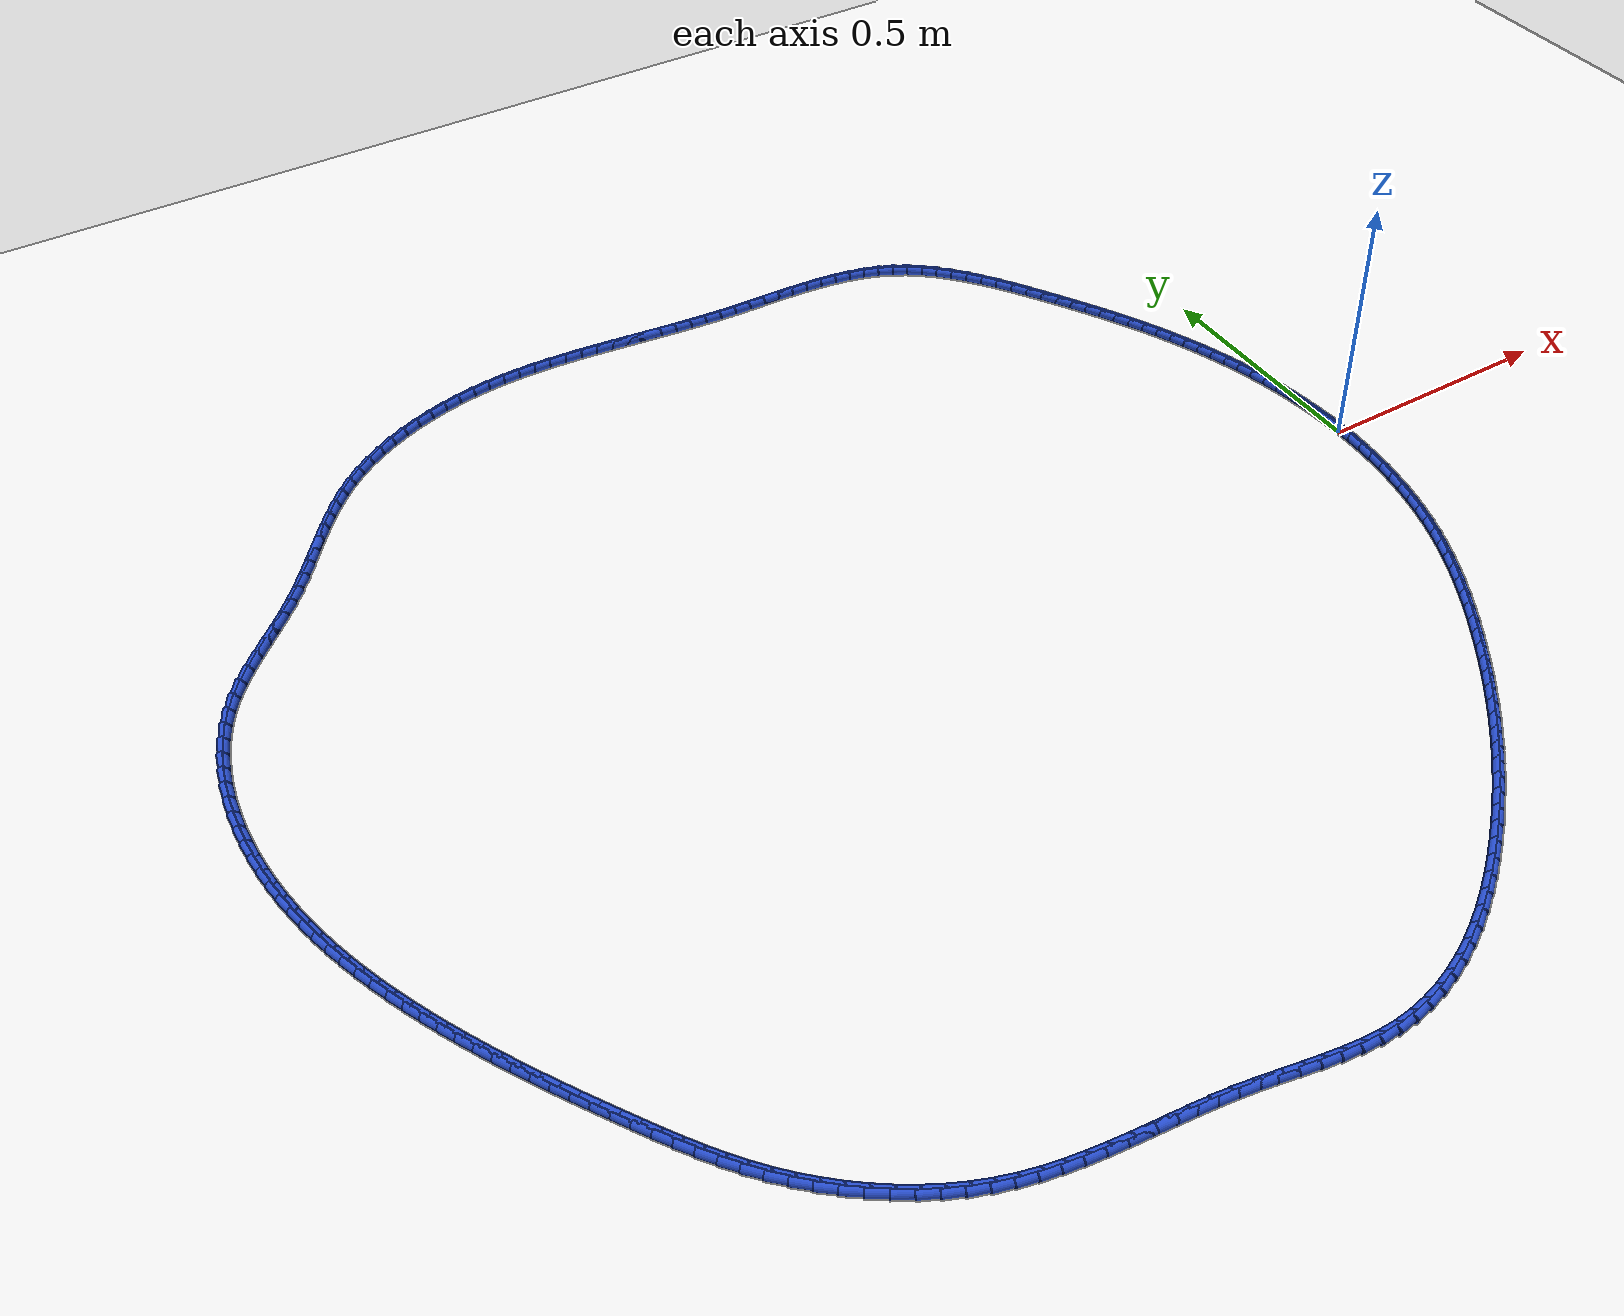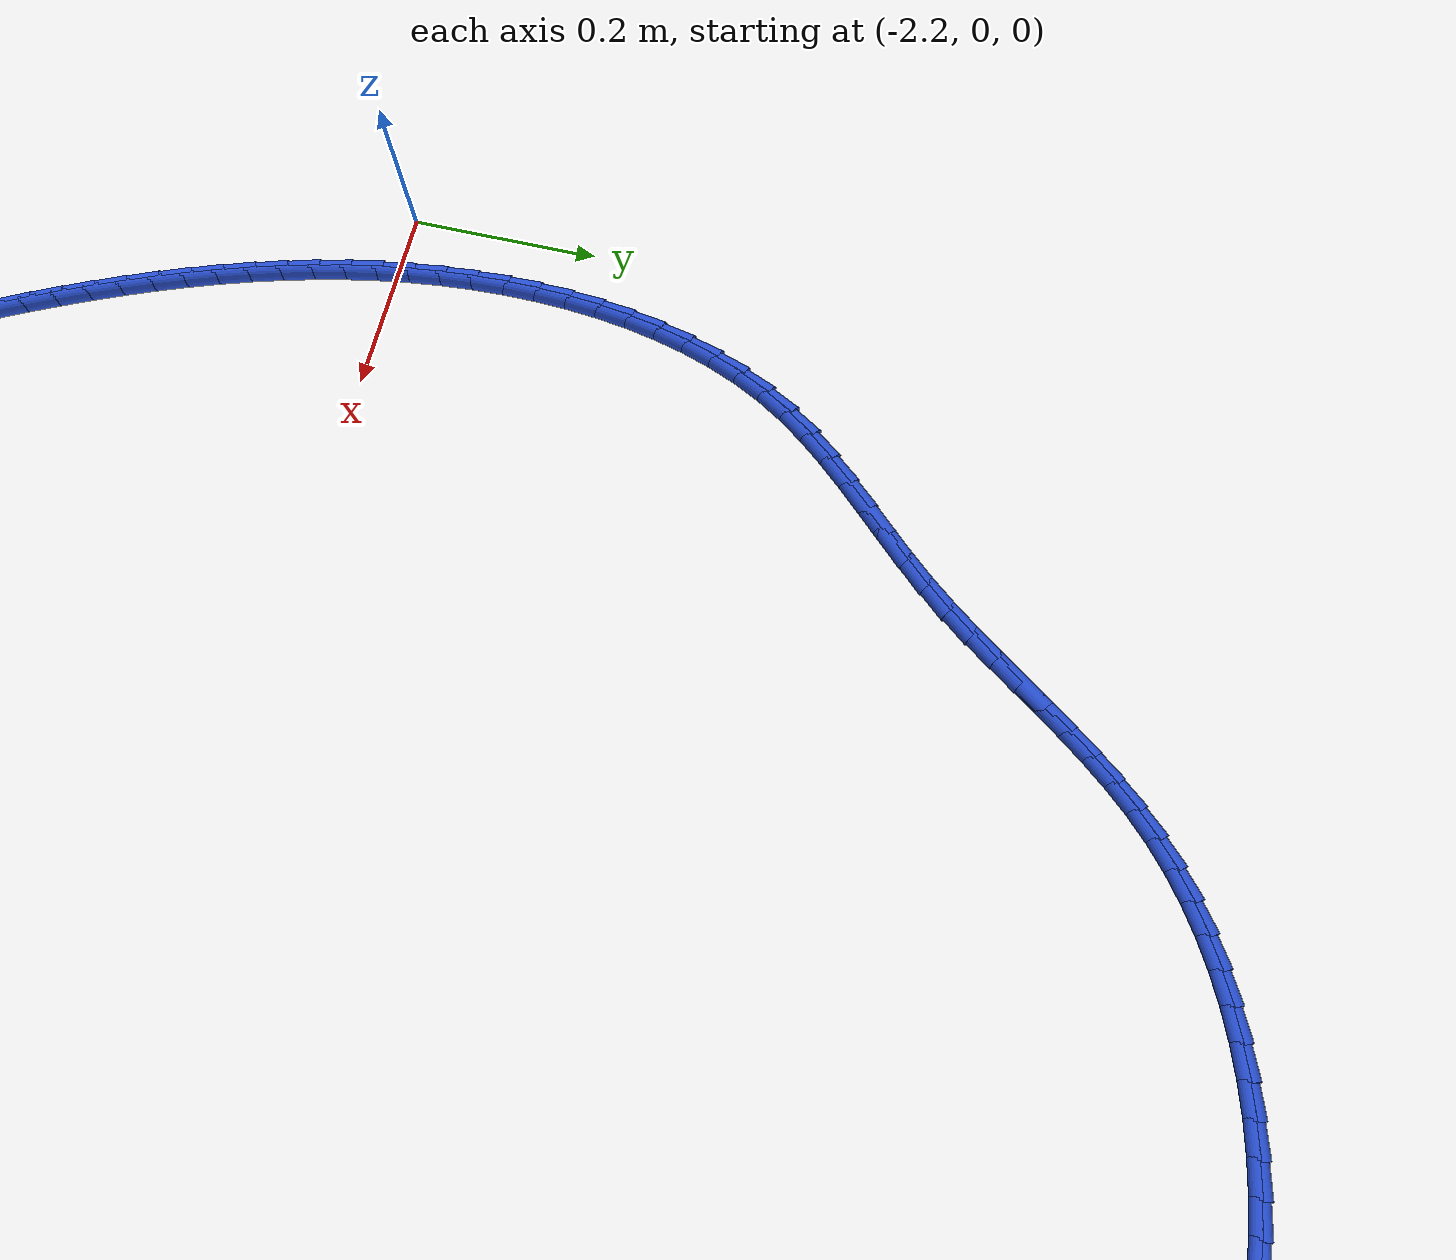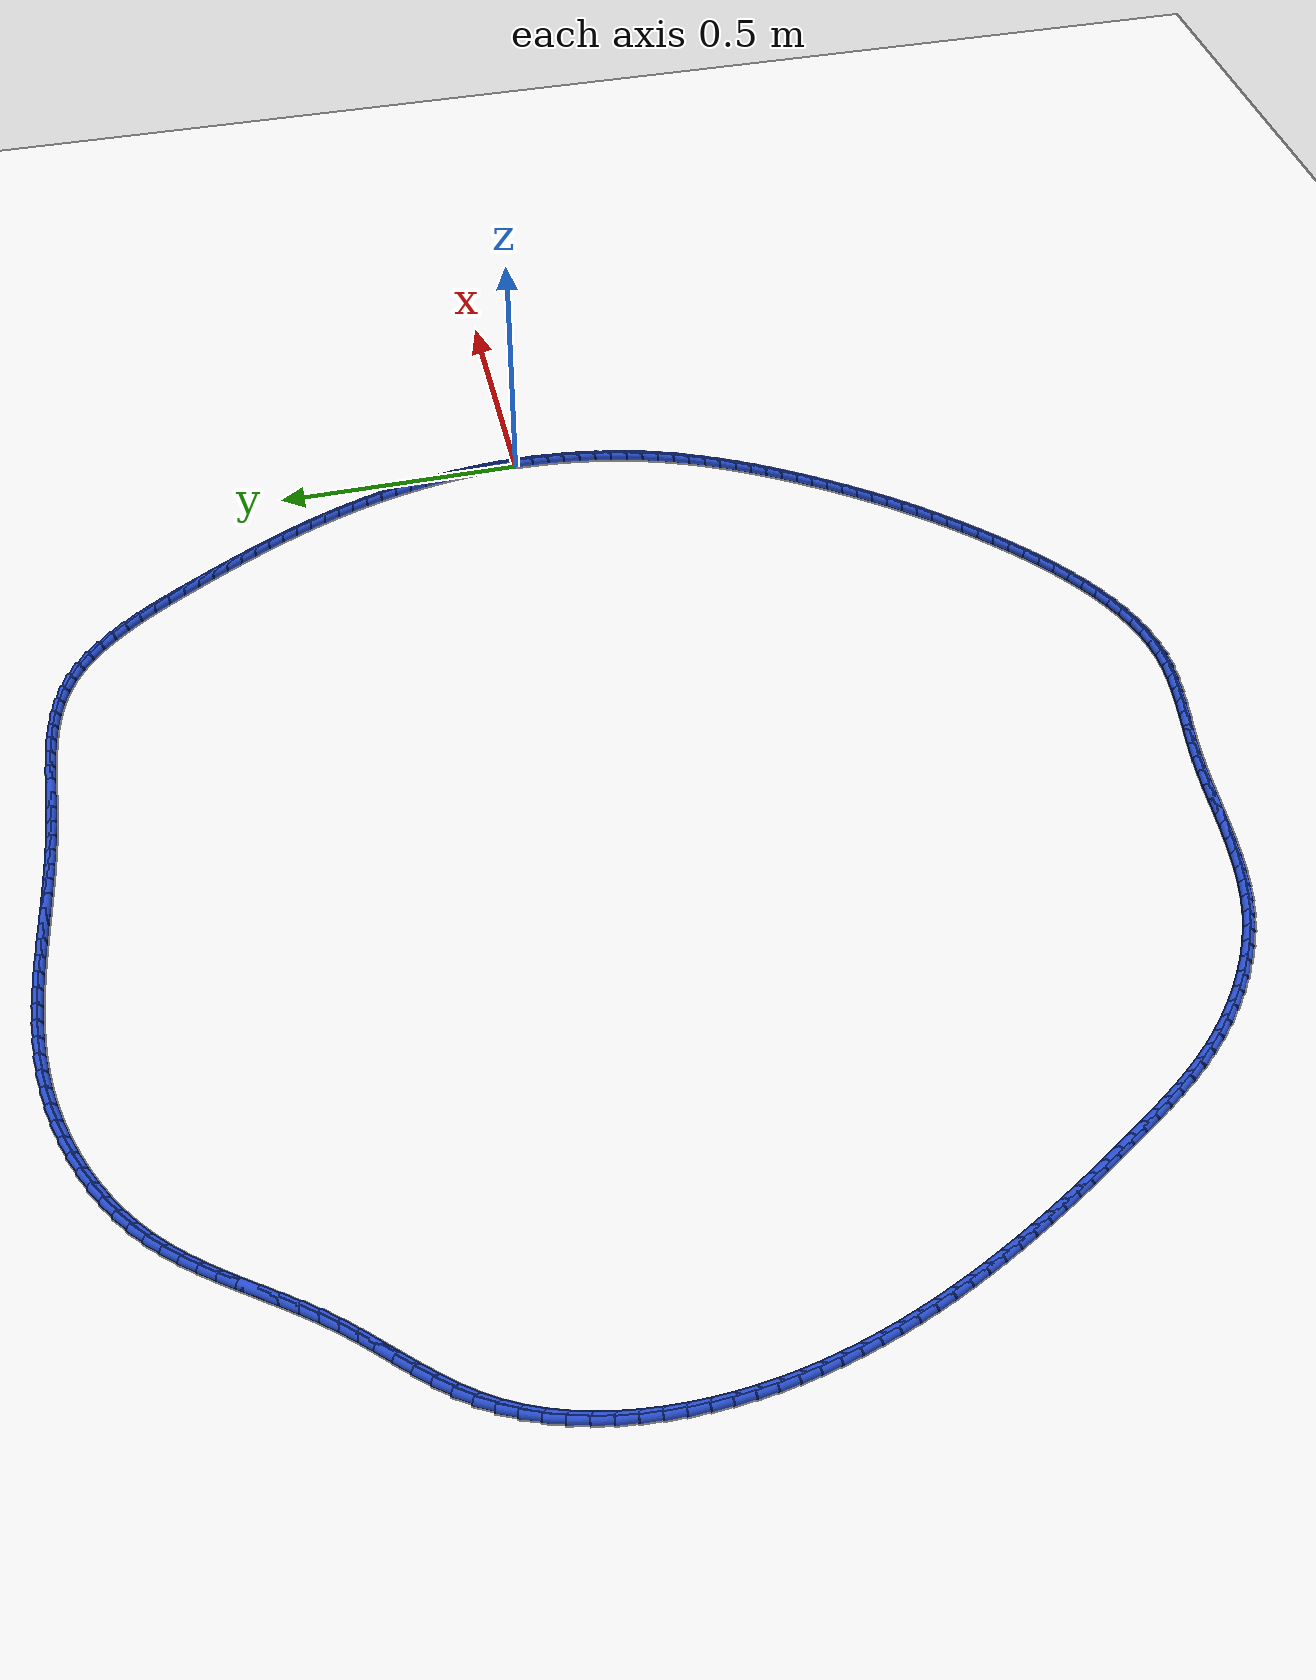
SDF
<sdf version="1.6">
 <world name="default">
  <light name="sun" type="directional">
   <pose>0 0 10 0 -0 0</pose>
   <diffuse>0.8 0.8 0.8 1</diffuse>
   <specular>0.2 0.2 0.2 1</specular>
   <attenuation>
    <range>1000</range>
    <constant>0.9</constant>
    <linear>0.01</linear>
    <quadratic>0.001</quadratic>
   </attenuation>
   <direction>-0.5 0.1 -0.9</direction>
  </light>
  <model name="ground_plane">
   <static>1</static>
   <link name="link">
    <collision name="collision">
     <geometry><plane><normal>0 0 1</normal><size>100 100</size></plane></geometry>
     <surface><friction><ode><mu>100</mu><mu2>50</mu2></ode></friction></surface>
    </collision>
    <visual name="visual">
     <cast_shadows>0</cast_shadows>
     <geometry><plane><normal>0 0 1</normal><size>100 100</size></plane></geometry>
     <material>
      <script><uri>file://media/materials/scripts/gazebo.material</uri><name>Gazebo/WhiteGlow</name></script>
     </material>
    </visual>
   </link>
  </model>
  <gravity>0 0 -9.8</gravity>
  <magnetic_field>6e-06 2.3e-05 -4.2e-05</magnetic_field>
  <atmosphere type="adiabatic"/>
  <physics name="default_physics" default="0" type="ode">
   <max_step_size>0.001</max_step_size>
   <real_time_factor>1</real_time_factor>
   <real_time_update_rate>1000</real_time_update_rate>
  </physics>
  <scene><ambient>0.4 0.4 0.4 1</ambient><background>0.7 0.7 0.7 1</background><shadows>1</shadows></scene>
  <spherical_coordinates>
   <surface_model>EARTH_WGS84</surface_model>
   <latitude_deg>0</latitude_deg>
   <longitude_deg>0</longitude_deg>
   <elevation>0</elevation>
   <heading_deg>0</heading_deg>
  </spherical_coordinates>
  <model name="line">
   <link name="link_0">
    <pose>3.122502256758253e-17 1.3877787807814457e-17 0.01 0 1.57 -1.545253485342555</pose>
    <collision name="collision">
     <geometry><cylinder><radius>0.01</radius><length>0.08</length></cylinder></geometry>
    </collision>
    <visual name="visual">
     <material>
      <script><name>Gazebo/Blue</name><uri>file://media/materials/scripts/gazebo.material</uri></script>
     </material>
     <geometry><cylinder><radius>0.01</radius><length>0.08</length></cylinder></geometry>
    </visual>
   </link>
   <link name="link_1">
    <pose>-0.000865920485348824 0.03389333795629715 0.01 0 1.57 -1.5114779695106455</pose>
    <collision name="collision">
     <geometry><cylinder><radius>0.01</radius><length>0.08</length></cylinder></geometry>
    </collision>
    <visual name="visual">
     <material>
      <script><name>Gazebo/Blue</name><uri>file://media/materials/scripts/gazebo.material</uri></script>
     </material>
     <geometry><cylinder><radius>0.01</radius><length>0.08</length></cylinder></geometry>
    </visual>
   </link>
   <link name="link_2">
    <pose>-0.002876116298317968 0.06774183974791337 0.01 0 1.57 -1.4786294431413702</pose>
    <collision name="collision">
     <geometry><cylinder><radius>0.01</radius><length>0.08</length></cylinder></geometry>
    </collision>
    <visual name="visual">
     <material>
      <script><name>Gazebo/Blue</name><uri>file://media/materials/scripts/gazebo.material</uri></script>
     </material>
     <geometry><cylinder><radius>0.01</radius><length>0.08</length></cylinder></geometry>
    </visual>
   </link>
   <link name="link_3">
    <pose>-0.005996338600805709 0.10149997519014346 0.01 0 1.57 -1.4466398844303219</pose>
    <collision name="collision">
     <geometry><cylinder><radius>0.01</radius><length>0.08</length></cylinder></geometry>
    </collision>
    <visual name="visual">
     <material>
      <script><name>Gazebo/Blue</name><uri>file://media/materials/scripts/gazebo.material</uri></script>
     </material>
     <geometry><cylinder><radius>0.01</radius><length>0.08</length></cylinder></geometry>
    </visual>
   </link>
   <link name="link_4">
    <pose>-0.010192338554710334 0.13512221409828223 0.01 0 1.57 -1.4154375836928796</pose>
    <collision name="collision">
     <geometry><cylinder><radius>0.01</radius><length>0.08</length></cylinder></geometry>
    </collision>
    <visual name="visual">
     <material>
      <script><name>Gazebo/Blue</name><uri>file://media/materials/scripts/gazebo.material</uri></script>
     </material>
     <geometry><cylinder><radius>0.01</radius><length>0.08</length></cylinder></geometry>
    </visual>
   </link>
   <link name="link_5">
    <pose>-0.015429867321930139 0.16856302628762446 0.01 0 1.57 -1.3849478388736798</pose>
    <collision name="collision">
     <geometry><cylinder><radius>0.01</radius><length>0.08</length></cylinder></geometry>
    </collision>
    <visual name="visual">
     <material>
      <script><name>Gazebo/Blue</name><uri>file://media/materials/scripts/gazebo.material</uri></script>
     </material>
     <geometry><cylinder><radius>0.01</radius><length>0.08</length></cylinder></geometry>
    </visual>
   </link>
   <link name="link_6">
    <pose>-0.021674676064363414 0.20177688157346502 0.01 0 1.57 -1.355093450607874</pose>
    <collision name="collision">
     <geometry><cylinder><radius>0.01</radius><length>0.08</length></cylinder></geometry>
    </collision>
    <visual name="visual">
     <material>
      <script><name>Gazebo/Blue</name><uri>file://media/materials/scripts/gazebo.material</uri></script>
     </material>
     <geometry><cylinder><radius>0.01</radius><length>0.08</length></cylinder></geometry>
    </visual>
   </link>
   <link name="link_7">
    <pose>-0.028892515943908466 0.23471824977109862 0.01 0 1.57 -1.3257950326625307</pose>
    <collision name="collision">
     <geometry><cylinder><radius>0.01</radius><length>0.08</length></cylinder></geometry>
    </collision>
    <visual name="visual">
     <material>
      <script><name>Gazebo/Blue</name><uri>file://media/materials/scripts/gazebo.material</uri></script>
     </material>
     <geometry><cylinder><radius>0.01</radius><length>0.08</length></cylinder></geometry>
    </visual>
   </link>
   <link name="link_8">
    <pose>-0.03704913812246359 0.26734160069582014 0.01 0 1.57 -1.2969711532674613</pose>
    <collision name="collision">
     <geometry><cylinder><radius>0.01</radius><length>0.08</length></cylinder></geometry>
    </collision>
    <visual name="visual">
     <material>
      <script><name>Gazebo/Blue</name><uri>file://media/materials/scripts/gazebo.material</uri></script>
     </material>
     <geometry><cylinder><radius>0.01</radius><length>0.08</length></cylinder></geometry>
    </visual>
   </link>
   <link name="link_9">
    <pose>-0.046110293761927074 0.2996014041629243 0.01 0 1.57 -1.2685850275636994</pose>
    <collision name="collision">
     <geometry><cylinder><radius>0.01</radius><length>0.08</length></cylinder></geometry>
    </collision>
    <visual name="visual">
     <material>
      <script><name>Gazebo/Blue</name><uri>file://media/materials/scripts/gazebo.material</uri></script>
     </material>
     <geometry><cylinder><radius>0.01</radius><length>0.08</length></cylinder></geometry>
    </visual>
   </link>
   <link name="link_10">
    <pose>-0.05604174847999134 0.33145741190993566 0.01 0 1.57 -1.2410812943710086</pose>
    <collision name="collision">
     <geometry><cylinder><radius>0.01</radius><length>0.08</length></cylinder></geometry>
    </collision>
    <visual name="visual">
     <material>
      <script><name>Gazebo/Blue</name><uri>file://media/materials/scripts/gazebo.material</uri></script>
     </material>
     <geometry><cylinder><radius>0.01</radius><length>0.08</length></cylinder></geometry>
    </visual>
   </link>
   <link name="link_11">
    <pose>-0.06680941415166988 0.3629228158236591 0.01 0 1.57 -1.214839223027288</pose>
    <collision name="collision">
     <geometry><cylinder><radius>0.01</radius><length>0.08</length></cylinder></geometry>
    </collision>
    <visual name="visual">
     <material>
      <script><name>Gazebo/Blue</name><uri>file://media/materials/scripts/gazebo.material</uri></script>
     </material>
     <geometry><cylinder><radius>0.01</radius><length>0.08</length></cylinder></geometry>
    </visual>
   </link>
   <link name="link_12">
    <pose>-0.078379287599311 0.39404184622518174 0.01 0 1.57 -1.189977491767885</pose>
    <collision name="collision">
     <geometry><cylinder><radius>0.01</radius><length>0.08</length></cylinder></geometry>
    </collision>
    <visual name="visual">
     <material>
      <script><name>Gazebo/Blue</name><uri>file://media/materials/scripts/gazebo.material</uri></script>
     </material>
     <geometry><cylinder><radius>0.01</radius><length>0.08</length></cylinder></geometry>
    </visual>
   </link>
   <link name="link_13">
    <pose>-0.09071736669249278 0.42485911607708055 0.01 0 1.57 -1.1665934481925826</pose>
    <collision name="collision">
     <geometry><cylinder><radius>0.01</radius><length>0.08</length></cylinder></geometry>
    </collision>
    <visual name="visual">
     <material>
      <script><name>Gazebo/Blue</name><uri>file://media/materials/scripts/gazebo.material</uri></script>
     </material>
     <geometry><cylinder><radius>0.01</radius><length>0.08</length></cylinder></geometry>
    </visual>
   </link>
   <link name="link_14">
    <pose>-0.10378964930079335 0.45541923834193215 0.01 0 1.57 -1.1447663570972086</pose>
    <collision name="collision">
     <geometry><cylinder><radius>0.01</radius><length>0.08</length></cylinder></geometry>
    </collision>
    <visual name="visual">
     <material>
      <script><name>Gazebo/Blue</name><uri>file://media/materials/scripts/gazebo.material</uri></script>
     </material>
     <geometry><cylinder><radius>0.01</radius><length>0.08</length></cylinder></geometry>
    </visual>
   </link>
   <link name="link_15">
    <pose>-0.11756213329379074 0.48576682598231335 0.01 0 1.57 -1.1245578417099682</pose>
    <collision name="collision">
     <geometry><cylinder><radius>0.01</radius><length>0.08</length></cylinder></geometry>
    </collision>
    <visual name="visual">
     <material>
      <script><name>Gazebo/Blue</name><uri>file://media/materials/scripts/gazebo.material</uri></script>
     </material>
     <geometry><cylinder><radius>0.01</radius><length>0.08</length></cylinder></geometry>
    </visual>
   </link>
   <link name="link_16">
    <pose>-0.1320008165410631 0.515946491960801 0.01 0 1.57 -1.1060127861267237</pose>
    <collision name="collision">
     <geometry><cylinder><radius>0.01</radius><length>0.08</length></cylinder></geometry>
    </collision>
    <visual name="visual">
     <material>
      <script><name>Gazebo/Blue</name><uri>file://media/materials/scripts/gazebo.material</uri></script>
     </material>
     <geometry><cylinder><radius>0.01</radius><length>0.08</length></cylinder></geometry>
    </visual>
   </link>
   <link name="link_17">
    <pose>-0.14707169691218863 0.546002849239972 0.01 0 1.57 -1.0891605754471807</pose>
    <collision name="collision">
     <geometry><cylinder><radius>0.01</radius><length>0.08</length></cylinder></geometry>
    </collision>
    <visual name="visual">
     <material>
      <script><name>Gazebo/Blue</name><uri>file://media/materials/scripts/gazebo.material</uri></script>
     </material>
     <geometry><cylinder><radius>0.01</radius><length>0.08</length></cylinder></geometry>
    </visual>
   </link>
   <link name="link_18">
    <pose>-0.16274077227674524 0.5759805107824028 0.01 0 1.57 -1.074016553728089</pose>
    <collision name="collision">
     <geometry><cylinder><radius>0.01</radius><length>0.08</length></cylinder></geometry>
    </collision>
    <visual name="visual">
     <material>
      <script><name>Gazebo/Blue</name><uri>file://media/materials/scripts/gazebo.material</uri></script>
     </material>
     <geometry><cylinder><radius>0.01</radius><length>0.08</length></cylinder></geometry>
    </visual>
   </link>
   <link name="link_19">
    <pose>-0.17897404050431126 0.6059240895506708 0.01 0 1.57 -1.0605835921100564</pose>
    <collision name="collision">
     <geometry><cylinder><radius>0.01</radius><length>0.08</length></cylinder></geometry>
    </collision>
    <visual name="visual">
     <material>
      <script><name>Gazebo/Blue</name><uri>file://media/materials/scripts/gazebo.material</uri></script>
     </material>
     <geometry><cylinder><radius>0.01</radius><length>0.08</length></cylinder></geometry>
    </visual>
   </link>
   <link name="link_20">
    <pose>-0.19573749946446461 0.6358781985073524 0.01 0 1.57 -1.0488536769395178</pose>
    <collision name="collision">
     <geometry><cylinder><radius>0.01</radius><length>0.08</length></cylinder></geometry>
    </collision>
    <visual name="visual">
     <material>
      <script><name>Gazebo/Blue</name><uri>file://media/materials/scripts/gazebo.material</uri></script>
     </material>
     <geometry><cylinder><radius>0.01</radius><length>0.08</length></cylinder></geometry>
    </visual>
   </link>
   <link name="link_21">
    <pose>-0.2129971470267834 0.6658874506150242 0.01 0 1.57 -1.038809447378384</pose>
    <collision name="collision">
     <geometry><cylinder><radius>0.01</radius><length>0.08</length></cylinder></geometry>
    </collision>
    <visual name="visual">
     <material>
      <script><name>Gazebo/Blue</name><uri>file://media/materials/scripts/gazebo.material</uri></script>
     </material>
     <geometry><cylinder><radius>0.01</radius><length>0.08</length></cylinder></geometry>
    </visual>
   </link>
   <link name="link_22">
    <pose>-0.2307189810608459 0.6959964588362635 0.01 0 1.57 -1.0293825329552073</pose>
    <collision name="collision">
     <geometry><cylinder><radius>0.01</radius><length>0.08</length></cylinder></geometry>
    </collision>
    <visual name="visual">
     <material>
      <script><name>Gazebo/Blue</name><uri>file://media/materials/scripts/gazebo.material</uri></script>
     </material>
     <geometry><cylinder><radius>0.01</radius><length>0.08</length></cylinder></geometry>
    </visual>
   </link>
   <link name="link_23">
    <pose>-0.24888639960591855 0.7262073617972887 0.01 0 1.57 -1.0143932947088314</pose>
    <collision name="collision">
     <geometry><cylinder><radius>0.01</radius><length>0.08</length></cylinder></geometry>
    </collision>
    <visual name="visual">
     <material>
      <script><name>Gazebo/Blue</name><uri>file://media/materials/scripts/gazebo.material</uri></script>
     </material>
     <geometry><cylinder><radius>0.01</radius><length>0.08</length></cylinder></geometry>
    </visual>
   </link>
   <link name="link_24">
    <pose>-0.26758524409550394 0.7562722307248411 0.01 0 1.57 -0.991416461137278</pose>
    <collision name="collision">
     <geometry><cylinder><radius>0.01</radius><length>0.08</length></cylinder></geometry>
    </collision>
    <visual name="visual">
     <material>
      <script><name>Gazebo/Blue</name><uri>file://media/materials/scripts/gazebo.material</uri></script>
     </material>
     <geometry><cylinder><radius>0.01</radius><length>0.08</length></cylinder></geometry>
    </visual>
   </link>
   <link name="link_25">
    <pose>-0.2869387212680915 0.7858519270149226 0.01 0 1.57 -0.960007470973449</pose>
    <collision name="collision">
     <geometry><cylinder><radius>0.01</radius><length>0.08</length></cylinder></geometry>
    </collision>
    <visual name="visual">
     <material>
      <script><name>Gazebo/Blue</name><uri>file://media/materials/scripts/gazebo.material</uri></script>
     </material>
     <geometry><cylinder><radius>0.01</radius><length>0.08</length></cylinder></geometry>
    </visual>
   </link>
   <link name="link_26">
    <pose>-0.30707009237589394 0.8146071789939 0.01 0 1.57 -0.9194810791921506</pose>
    <collision name="collision">
     <geometry><cylinder><radius>0.01</radius><length>0.08</length></cylinder></geometry>
    </collision>
    <visual name="visual">
     <material>
      <script><name>Gazebo/Blue</name><uri>file://media/materials/scripts/gazebo.material</uri></script>
     </material>
     <geometry><cylinder><radius>0.01</radius><length>0.08</length></cylinder></geometry>
    </visual>
   </link>
   <link name="link_27">
    <pose>-0.328102618671124 0.8421987149881404 0.01 0 1.57 -0.8689412261048902</pose>
    <collision name="collision">
     <geometry><cylinder><radius>0.01</radius><length>0.08</length></cylinder></geometry>
    </collision>
    <visual name="visual">
     <material>
      <script><name>Gazebo/Blue</name><uri>file://media/materials/scripts/gazebo.material</uri></script>
     </material>
     <geometry><cylinder><radius>0.01</radius><length>0.08</length></cylinder></geometry>
    </visual>
   </link>
   <link name="link_28">
    <pose>-0.35015956140599436 0.8682872633240108 0.01 0 1.57 -0.8073471904289259</pose>
    <collision name="collision">
     <geometry><cylinder><radius>0.01</radius><length>0.08</length></cylinder></geometry>
    </collision>
    <visual name="visual">
     <material>
      <script><name>Gazebo/Blue</name><uri>file://media/materials/scripts/gazebo.material</uri></script>
     </material>
     <geometry><cylinder><radius>0.01</radius><length>0.08</length></cylinder></geometry>
    </visual>
   </link>
   <link name="link_29">
    <pose>-0.3733641818327177 0.892533552327878 0.01 0 1.57 -0.7336441424200234</pose>
    <collision name="collision">
     <geometry><cylinder><radius>0.01</radius><length>0.08</length></cylinder></geometry>
    </collision>
    <visual name="visual">
     <material>
      <script><name>Gazebo/Blue</name><uri>file://media/materials/scripts/gazebo.material</uri></script>
     </material>
     <geometry><cylinder><radius>0.01</radius><length>0.08</length></cylinder></geometry>
    </visual>
   </link>
   <link name="link_30">
    <pose>-0.3978397412035066 0.9145983103261094 0.01 0 1.57 -0.6469958784442206</pose>
    <collision name="collision">
     <geometry><cylinder><radius>0.01</radius><length>0.08</length></cylinder></geometry>
    </collision>
    <visual name="visual">
     <material>
      <script><name>Gazebo/Blue</name><uri>file://media/materials/scripts/gazebo.material</uri></script>
     </material>
     <geometry><cylinder><radius>0.01</radius><length>0.08</length></cylinder></geometry>
    </visual>
   </link>
   <link name="link_31">
    <pose>-0.4237095007705741 0.9341422656450717 0.01 0 1.57 -0.5471457314248681</pose>
    <collision name="collision">
     <geometry><cylinder><radius>0.01</radius><length>0.08</length></cylinder></geometry>
    </collision>
    <visual name="visual">
     <material>
      <script><name>Gazebo/Blue</name><uri>file://media/materials/scripts/gazebo.material</uri></script>
     </material>
     <geometry><cylinder><radius>0.01</radius><length>0.08</length></cylinder></geometry>
    </visual>
   </link>
   <link name="link_32">
    <pose>-0.45109672178613264 0.9508261466111319 0.01 0 1.57 -0.438390828728084</pose>
    <collision name="collision">
     <geometry><cylinder><radius>0.01</radius><length>0.08</length></cylinder></geometry>
    </collision>
    <visual name="visual">
     <material>
      <script><name>Gazebo/Blue</name><uri>file://media/materials/scripts/gazebo.material</uri></script>
     </material>
     <geometry><cylinder><radius>0.01</radius><length>0.08</length></cylinder></geometry>
    </visual>
   </link>
   <link name="link_33">
    <pose>-0.48007790197268224 0.9644129932289268 0.01 0 1.57 -0.33855191756990594</pose>
    <collision name="collision">
     <geometry><cylinder><radius>0.01</radius><length>0.08</length></cylinder></geometry>
    </collision>
    <visual name="visual">
     <material>
      <script><name>Gazebo/Blue</name><uri>file://media/materials/scripts/gazebo.material</uri></script>
     </material>
     <geometry><cylinder><radius>0.01</radius><length>0.08</length></cylinder></geometry>
    </visual>
   </link>
   <link name="link_34">
    <pose>-0.5105169973305816 0.9751308553179726 0.01 0 1.57 -0.25338710884146065</pose>
    <collision name="collision">
     <geometry><cylinder><radius>0.01</radius><length>0.08</length></cylinder></geometry>
    </collision>
    <visual name="visual">
     <material>
      <script><name>Gazebo/Blue</name><uri>file://media/materials/scripts/gazebo.material</uri></script>
     </material>
     <geometry><cylinder><radius>0.01</radius><length>0.08</length></cylinder></geometry>
    </visual>
   </link>
   <link name="link_35">
    <pose>-0.5422176115466872 0.9833398246227556 0.01 0 1.57 -0.18288799391079796</pose>
    <collision name="collision">
     <geometry><cylinder><radius>0.01</radius><length>0.08</length></cylinder></geometry>
    </collision>
    <visual name="visual">
     <material>
      <script><name>Gazebo/Blue</name><uri>file://media/materials/scripts/gazebo.material</uri></script>
     </material>
     <geometry><cylinder><radius>0.01</radius><length>0.08</length></cylinder></geometry>
    </visual>
   </link>
   <link name="link_36">
    <pose>-0.5749833442077475 0.9894000018581951 0.01 0 1.57 -0.12632112361747572</pose>
    <collision name="collision">
     <geometry><cylinder><radius>0.01</radius><length>0.08</length></cylinder></geometry>
    </collision>
    <visual name="visual">
     <material>
      <script><name>Gazebo/Blue</name><uri>file://media/materials/scripts/gazebo.material</uri></script>
     </material>
     <geometry><cylinder><radius>0.01</radius><length>0.08</length></cylinder></geometry>
    </visual>
   </link>
   <link name="link_37">
    <pose>-0.6086177949005109 0.9936714877392103 0.01 0 1.57 -0.08267798887693112</pose>
    <collision name="collision">
     <geometry><cylinder><radius>0.01</radius><length>0.08</length></cylinder></geometry>
    </collision>
    <visual name="visual">
     <material>
      <script><name>Gazebo/Blue</name><uri>file://media/materials/scripts/gazebo.material</uri></script>
     </material>
     <geometry><cylinder><radius>0.01</radius><length>0.08</length></cylinder></geometry>
    </visual>
   </link>
   <link name="link_38">
    <pose>-0.6429245632117258 0.9965143829807198 0.01 0 1.57 -0.050969855635384434</pose>
    <collision name="collision">
     <geometry><cylinder><radius>0.01</radius><length>0.08</length></cylinder></geometry>
    </collision>
    <visual name="visual">
     <material>
      <script><name>Gazebo/Blue</name><uri>file://media/materials/scripts/gazebo.material</uri></script>
     </material>
     <geometry><cylinder><radius>0.01</radius><length>0.08</length></cylinder></geometry>
    </visual>
   </link>
   <link name="link_39">
    <pose>-0.67770724872814 0.9982887882976427 0.01 0 1.57 -0.030394206644511312</pose>
    <collision name="collision">
     <geometry><cylinder><radius>0.01</radius><length>0.08</length></cylinder></geometry>
    </collision>
    <visual name="visual">
     <material>
      <script><name>Gazebo/Blue</name><uri>file://media/materials/scripts/gazebo.material</uri></script>
     </material>
     <geometry><cylinder><radius>0.01</radius><length>0.08</length></cylinder></geometry>
    </visual>
   </link>
   <link name="link_40">
    <pose>-0.7127694510365022 0.9993548044048974 0.01 0 1.57 -0.020418874804474532</pose>
    <collision name="collision">
     <geometry><cylinder><radius>0.01</radius><length>0.08</length></cylinder></geometry>
    </collision>
    <visual name="visual">
     <material>
      <script><name>Gazebo/Blue</name><uri>file://media/materials/scripts/gazebo.material</uri></script>
     </material>
     <geometry><cylinder><radius>0.01</radius><length>0.08</length></cylinder></geometry>
    </visual>
   </link>
   <link name="link_41">
    <pose>-0.7479147697235604 1.0000725320174029 0.01 0 1.57 -0.020821925005947522</pose>
    <collision name="collision">
     <geometry><cylinder><radius>0.01</radius><length>0.08</length></cylinder></geometry>
    </collision>
    <visual name="visual">
     <material>
      <script><name>Gazebo/Blue</name><uri>file://media/materials/scripts/gazebo.material</uri></script>
     </material>
     <geometry><cylinder><radius>0.01</radius><length>0.08</length></cylinder></geometry>
    </visual>
   </link>
   <link name="link_42">
    <pose>-0.7829468043760627 1.000802071850078 0.01 0 1.57 -0.03171108902651052</pose>
    <collision name="collision">
     <geometry><cylinder><radius>0.01</radius><length>0.08</length></cylinder></geometry>
    </collision>
    <visual name="visual">
     <material>
      <script><name>Gazebo/Blue</name><uri>file://media/materials/scripts/gazebo.material</uri></script>
     </material>
     <geometry><cylinder><radius>0.01</radius><length>0.08</length></cylinder></geometry>
    </visual>
   </link>
   <link name="link_43">
    <pose>-0.8176691545807574 1.0019035246178416 0.01 0 1.57 -0.05137869679514244</pose>
    <collision name="collision">
     <geometry><cylinder><radius>0.01</radius><length>0.08</length></cylinder></geometry>
    </collision>
    <visual name="visual">
     <material>
      <script><name>Gazebo/Blue</name><uri>file://media/materials/scripts/gazebo.material</uri></script>
     </material>
     <geometry><cylinder><radius>0.01</radius><length>0.08</length></cylinder></geometry>
    </visual>
   </link>
   <link name="link_44">
    <pose>-0.8519303172179651 1.0036653690660475 0.01 0 1.57 -0.07068711061122268</pose>
    <collision name="collision">
     <geometry><cylinder><radius>0.01</radius><length>0.08</length></cylinder></geometry>
    </collision>
    <visual name="visual">
     <material>
      <script><name>Gazebo/Blue</name><uri>file://media/materials/scripts/gazebo.material</uri></script>
     </material>
     <geometry><cylinder><radius>0.01</radius><length>0.08</length></cylinder></geometry>
    </visual>
   </link>
   <link name="link_45">
    <pose>-0.8857758018963304 1.0060618013071914 0.01 0 1.57 -0.08684018985515787</pose>
    <collision name="collision">
     <geometry><cylinder><radius>0.01</radius><length>0.08</length></cylinder></geometry>
    </collision>
    <visual name="visual">
     <material>
      <script><name>Gazebo/Blue</name><uri>file://media/materials/scripts/gazebo.material</uri></script>
     </material>
     <geometry><cylinder><radius>0.01</radius><length>0.08</length></cylinder></geometry>
    </visual>
   </link>
   <link name="link_46">
    <pose>-0.9193051417613309 1.0089808369336768 0.01 0 1.57 -0.09962048377111418</pose>
    <collision name="collision">
     <geometry><cylinder><radius>0.01</radius><length>0.08</length></cylinder></geometry>
    </collision>
    <visual name="visual">
     <material>
      <script><name>Gazebo/Blue</name><uri>file://media/materials/scripts/gazebo.material</uri></script>
     </material>
     <geometry><cylinder><radius>0.01</radius><length>0.08</length></cylinder></geometry>
    </visual>
   </link>
   <link name="link_47">
    <pose>-0.9526178714063661 1.0123104892281218 0.01 0 1.57 -0.10886776145703458</pose>
    <collision name="collision">
     <geometry><cylinder><radius>0.01</radius><length>0.08</length></cylinder></geometry>
    </collision>
    <visual name="visual">
     <material>
      <script><name>Gazebo/Blue</name><uri>file://media/materials/scripts/gazebo.material</uri></script>
     </material>
     <geometry><cylinder><radius>0.01</radius><length>0.08</length></cylinder></geometry>
    </visual>
   </link>
   <link name="link_48">
    <pose>-0.9858135254248359 1.0159387714731445 0.01 0 1.57 -0.11448044236311579</pose>
    <collision name="collision">
     <geometry><cylinder><radius>0.01</radius><length>0.08</length></cylinder></geometry>
    </collision>
    <visual name="visual">
     <material>
      <script><name>Gazebo/Blue</name><uri>file://media/materials/scripts/gazebo.material</uri></script>
     </material>
     <geometry><cylinder><radius>0.01</radius><length>0.08</length></cylinder></geometry>
    </visual>
   </link>
   <link name="link_49">
    <pose>-1.0189916384101403 1.019753696951363 0.01 0 1.57 -0.11638283449637628</pose>
    <collision name="collision">
     <geometry><cylinder><radius>0.01</radius><length>0.08</length></cylinder></geometry>
    </collision>
    <visual name="visual">
     <material>
      <script><name>Gazebo/Blue</name><uri>file://media/materials/scripts/gazebo.material</uri></script>
     </material>
     <geometry><cylinder><radius>0.01</radius><length>0.08</length></cylinder></geometry>
    </visual>
   </link>
   <link name="link_50">
    <pose>-1.0522493299442428 1.0236418923896087 0.01 0 1.57 -0.11383761230035552</pose>
    <collision name="collision">
     <geometry><cylinder><radius>0.01</radius><length>0.08</length></cylinder></geometry>
    </collision>
    <visual name="visual">
     <material>
      <script><name>Gazebo/Blue</name><uri>file://media/materials/scripts/gazebo.material</uri></script>
     </material>
     <geometry><cylinder><radius>0.01</radius><length>0.08</length></cylinder></geometry>
    </visual>
   </link>
   <link name="link_51">
    <pose>-1.0856283176021684 1.027458175980729 0.01 0 1.57 -0.10613242274218272</pose>
    <collision name="collision">
     <geometry><cylinder><radius>0.01</radius><length>0.08</length></cylinder></geometry>
    </collision>
    <visual name="visual">
     <material>
      <script><name>Gazebo/Blue</name><uri>file://media/materials/scripts/gazebo.material</uri></script>
     </material>
     <geometry><cylinder><radius>0.01</radius><length>0.08</length></cylinder></geometry>
    </visual>
   </link>
   <link name="link_52">
    <pose>-1.1191149964220675 1.0310256030105693 0.01 0 1.57 -0.09324876672268698</pose>
    <collision name="collision">
     <geometry><cylinder><radius>0.01</radius><length>0.08</length></cylinder></geometry>
    </collision>
    <visual name="visual">
     <material>
      <script><name>Gazebo/Blue</name><uri>file://media/materials/scripts/gazebo.material</uri></script>
     </material>
     <geometry><cylinder><radius>0.01</radius><length>0.08</length></cylinder></geometry>
    </visual>
   </link>
   <link name="link_53">
    <pose>-1.1526933623246747 1.0341658513345873 0.01 0 1.57 -0.0751758197110959</pose>
    <collision name="collision">
     <geometry><cylinder><radius>0.01</radius><length>0.08</length></cylinder></geometry>
    </collision>
    <visual name="visual">
     <material>
      <script><name>Gazebo/Blue</name><uri>file://media/materials/scripts/gazebo.material</uri></script>
     </material>
     <geometry><cylinder><radius>0.01</radius><length>0.08</length></cylinder></geometry>
    </visual>
   </link>
   <link name="link_54">
    <pose>-1.186347411230725 1.0367005988082412 0.01 0 1.57 -0.05188844149849733</pose>
    <collision name="collision">
     <geometry><cylinder><radius>0.01</radius><length>0.08</length></cylinder></geometry>
    </collision>
    <visual name="visual">
     <material>
      <script><name>Gazebo/Blue</name><uri>file://media/materials/scripts/gazebo.material</uri></script>
     </material>
     <geometry><cylinder><radius>0.01</radius><length>0.08</length></cylinder></geometry>
    </visual>
   </link>
   <link name="link_55">
    <pose>-1.2200611390609535 1.0384515232869886 0.01 0 1.57 -0.02336186354582435</pose>
    <collision name="collision">
     <geometry><cylinder><radius>0.01</radius><length>0.08</length></cylinder></geometry>
    </collision>
    <visual name="visual">
     <material>
      <script><name>Gazebo/Blue</name><uri>file://media/materials/scripts/gazebo.material</uri></script>
     </material>
     <geometry><cylinder><radius>0.01</radius><length>0.08</length></cylinder></geometry>
    </visual>
   </link>
   <link name="link_56">
    <pose>-1.2538185417360947 1.0392403026262882 0.01 0 1.57 0.010409189823853237</pose>
    <collision name="collision">
     <geometry><cylinder><radius>0.01</radius><length>0.08</length></cylinder></geometry>
    </collision>
    <visual name="visual">
     <material>
      <script><name>Gazebo/Blue</name><uri>file://media/materials/scripts/gazebo.material</uri></script>
     </material>
     <geometry><cylinder><radius>0.01</radius><length>0.08</length></cylinder></geometry>
    </visual>
   </link>
   <link name="link_57">
    <pose>-1.287603615176884 1.0388886146815977 0.01 0 1.57 0.049386982493541724</pose>
    <collision name="collision">
     <geometry><cylinder><radius>0.01</radius><length>0.08</length></cylinder></geometry>
    </collision>
    <visual name="visual">
     <material>
      <script><name>Gazebo/Blue</name><uri>file://media/materials/scripts/gazebo.material</uri></script>
     </material>
     <geometry><cylinder><radius>0.01</radius><length>0.08</length></cylinder></geometry>
    </visual>
   </link>
   <link name="link_58">
    <pose>-1.3214003553040552 1.037218137308375 0.01 0 1.57 0.09346361546736663</pose>
    <collision name="collision">
     <geometry><cylinder><radius>0.01</radius><length>0.08</length></cylinder></geometry>
    </collision>
    <visual name="visual">
     <material>
      <script><name>Gazebo/Blue</name><uri>file://media/materials/scripts/gazebo.material</uri></script>
     </material>
     <geometry><cylinder><radius>0.01</radius><length>0.08</length></cylinder></geometry>
    </visual>
   </link>
   <link name="link_59">
    <pose>-1.355192758038344 1.0340505483620785 0.01 0 1.57 0.1423576001768085</pose>
    <collision name="collision">
     <geometry><cylinder><radius>0.01</radius><length>0.08</length></cylinder></geometry>
    </collision>
    <visual name="visual">
     <material>
      <script><name>Gazebo/Blue</name><uri>file://media/materials/scripts/gazebo.material</uri></script>
     </material>
     <geometry><cylinder><radius>0.01</radius><length>0.08</length></cylinder></geometry>
    </visual>
   </link>
   <link name="link_60">
    <pose>-1.388962610846772 1.0292104126745438 0.01 0 1.57 0.19366673334273485</pose>
    <collision name="collision">
     <geometry><cylinder><radius>0.01</radius><length>0.08</length></cylinder></geometry>
    </collision>
    <visual name="visual">
     <material>
      <script><name>Gazebo/Blue</name><uri>file://media/materials/scripts/gazebo.material</uri></script>
     </material>
     <geometry><cylinder><radius>0.01</radius><length>0.08</length></cylinder></geometry>
    </visual>
   </link>
   <link name="link_61">
    <pose>-1.4226259983181357 1.022608184429128 0.01 0 1.57 0.2451497310486619</pose>
    <collision name="collision">
     <geometry><cylinder><radius>0.01</radius><length>0.08</length></cylinder></geometry>
    </collision>
    <visual name="visual">
     <material>
      <script><name>Gazebo/Blue</name><uri>file://media/materials/scripts/gazebo.material</uri></script>
     </material>
     <geometry><cylinder><radius>0.01</radius><length>0.08</length></cylinder></geometry>
    </visual>
   </link>
   <link name="link_62">
    <pose>-1.4560237672498184 1.014252671569169 0.01 0 1.57 0.29712200238520126</pose>
    <collision name="collision">
     <geometry><cylinder><radius>0.01</radius><length>0.08</length></cylinder></geometry>
    </collision>
    <visual name="visual">
     <material>
      <script><name>Gazebo/Blue</name><uri>file://media/materials/scripts/gazebo.material</uri></script>
     </material>
     <geometry><cylinder><radius>0.01</radius><length>0.08</length></cylinder></geometry>
    </visual>
   </link>
   <link name="link_63">
    <pose>-1.4889926380186396 1.004158076255058 0.01 0 1.57 0.3500288925562885</pose>
    <collision name="collision">
     <geometry><cylinder><radius>0.01</radius><length>0.08</length></cylinder></geometry>
    </collision>
    <visual name="visual">
     <material>
      <script><name>Gazebo/Blue</name><uri>file://media/materials/scripts/gazebo.material</uri></script>
     </material>
     <geometry><cylinder><radius>0.01</radius><length>0.08</length></cylinder></geometry>
    </visual>
   </link>
   <link name="link_64">
    <pose>-1.5213693310014196 0.9923386006471859 0.01 0 1.57 0.4043090916482738</pose>
    <collision name="collision">
     <geometry><cylinder><radius>0.01</radius><length>0.08</length></cylinder></geometry>
    </collision>
    <visual name="visual">
     <material>
      <script><name>Gazebo/Blue</name><uri>file://media/materials/scripts/gazebo.material</uri></script>
     </material>
     <geometry><cylinder><radius>0.01</radius><length>0.08</length></cylinder></geometry>
    </visual>
   </link>
   <link name="link_65">
    <pose>-1.5529905665749777 0.978808446905944 0.01 0 1.57 0.46039518902360194</pose>
    <collision name="collision">
     <geometry><cylinder><radius>0.01</radius><length>0.08</length></cylinder></geometry>
    </collision>
    <visual name="visual">
     <material>
      <script><name>Gazebo/Blue</name><uri>file://media/materials/scripts/gazebo.material</uri></script>
     </material>
     <geometry><cylinder><radius>0.01</radius><length>0.08</length></cylinder></geometry>
    </visual>
   </link>
   <link name="link_66">
    <pose>-1.5836930651161345 0.9635818171917236 0.01 0 1.57 0.518711161567841</pose>
    <collision name="collision">
     <geometry><cylinder><radius>0.01</radius><length>0.08</length></cylinder></geometry>
    </collision>
    <visual name="visual">
     <material>
      <script><name>Gazebo/Blue</name><uri>file://media/materials/scripts/gazebo.material</uri></script>
     </material>
     <geometry><cylinder><radius>0.01</radius><length>0.08</length></cylinder></geometry>
    </visual>
   </link>
   <link name="link_67">
    <pose>-1.6133135470017104 0.9466729136649163 0.01 0 1.57 0.5796657850404748</pose>
    <collision name="collision">
     <geometry><cylinder><radius>0.01</radius><length>0.08</length></cylinder></geometry>
    </collision>
    <visual name="visual">
     <material>
      <script><name>Gazebo/Blue</name><uri>file://media/materials/scripts/gazebo.material</uri></script>
     </material>
     <geometry><cylinder><radius>0.01</radius><length>0.08</length></cylinder></geometry>
    </visual>
   </link>
   <link name="link_68">
    <pose>-1.6416887326085237 0.9280959384859125 0.01 0 1.57 0.6436408199464149</pose>
    <collision name="collision">
     <geometry><cylinder><radius>0.01</radius><length>0.08</length></cylinder></geometry>
    </collision>
    <visual name="visual">
     <material>
      <script><name>Gazebo/Blue</name><uri>file://media/materials/scripts/gazebo.material</uri></script>
     </material>
     <geometry><cylinder><radius>0.01</radius><length>0.08</length></cylinder></geometry>
    </visual>
   </link>
   <link name="link_69">
    <pose>-1.6686553423133956 0.907865093815104 0.01 0 1.57 0.7109728405221866</pose>
    <collision name="collision">
     <geometry><cylinder><radius>0.01</radius><length>0.08</length></cylinder></geometry>
    </collision>
    <visual name="visual">
     <material>
      <script><name>Gazebo/Blue</name><uri>file://media/materials/scripts/gazebo.material</uri></script>
     </material>
     <geometry><cylinder><radius>0.01</radius><length>0.08</length></cylinder></geometry>
    </visual>
   </link>
   <link name="link_70">
    <pose>-1.6940500964931466 0.8859945818128819 0.01 0 1.57 0.7796283577404893</pose>
    <collision name="collision">
     <geometry><cylinder><radius>0.01</radius><length>0.08</length></cylinder></geometry>
    </collision>
    <visual name="visual">
     <material>
      <script><name>Gazebo/Blue</name><uri>file://media/materials/scripts/gazebo.material</uri></script>
     </material>
     <geometry><cylinder><radius>0.01</radius><length>0.08</length></cylinder></geometry>
    </visual>
   </link>
   <link name="link_71">
    <pose>-1.7177804052226917 0.8625365436952807 0.01 0 1.57 0.8394597505369964</pose>
    <collision name="collision">
     <geometry><cylinder><radius>0.01</radius><length>0.08</length></cylinder></geometry>
    </collision>
    <visual name="visual">
     <material>
      <script><name>Gazebo/Blue</name><uri>file://media/materials/scripts/gazebo.material</uri></script>
     </material>
     <geometry><cylinder><radius>0.01</radius><length>0.08</length></cylinder></geometry>
    </visual>
   </link>
   <link name="link_72">
    <pose>-1.7400601123426067 0.837707583223785 0.01 0 1.57 0.8873023868798748</pose>
    <collision name="collision">
     <geometry><cylinder><radius>0.01</radius><length>0.08</length></cylinder></geometry>
    </collision>
    <visual name="visual">
     <material>
      <script><name>Gazebo/Blue</name><uri>file://media/materials/scripts/gazebo.material</uri></script>
     </material>
     <geometry><cylinder><radius>0.01</radius><length>0.08</length></cylinder></geometry>
    </visual>
   </link>
   <link name="link_73">
    <pose>-1.7611860761815306 0.8117688579119363 0.01 0 1.57 0.9230422042411489</pose>
    <collision name="collision">
     <geometry><cylinder><radius>0.01</radius><length>0.08</length></cylinder></geometry>
    </collision>
    <visual name="visual">
     <material>
      <script><name>Gazebo/Blue</name><uri>file://media/materials/scripts/gazebo.material</uri></script>
     </material>
     <geometry><cylinder><radius>0.01</radius><length>0.08</length></cylinder></geometry>
    </visual>
   </link>
   <link name="link_74">
    <pose>-1.781455156542857 0.784981526064774 0.01 0 1.57 0.9467921590086865</pose>
    <collision name="collision">
     <geometry><cylinder><radius>0.01</radius><length>0.08</length></cylinder></geometry>
    </collision>
    <visual name="visual">
     <material>
      <script><name>Gazebo/Blue</name><uri>file://media/materials/scripts/gazebo.material</uri></script>
     </material>
     <geometry><cylinder><radius>0.01</radius><length>0.08</length></cylinder></geometry>
    </visual>
   </link>
   <link name="link_75">
    <pose>-1.8011642132299828 0.7576067459873387 0.01 0 1.57 0.9587355883283306</pose>
    <collision name="collision">
     <geometry><cylinder><radius>0.01</radius><length>0.08</length></cylinder></geometry>
    </collision>
    <visual name="visual">
     <material>
      <script><name>Gazebo/Blue</name><uri>file://media/materials/scripts/gazebo.material</uri></script>
     </material>
     <geometry><cylinder><radius>0.01</radius><length>0.08</length></cylinder></geometry>
    </visual>
   </link>
   <link name="link_76">
    <pose>-1.8206101060463031 0.7299056759846706 0.01 0 1.57 0.9590257827410408</pose>
    <collision name="collision">
     <geometry><cylinder><radius>0.01</radius><length>0.08</length></cylinder></geometry>
    </collision>
    <visual name="visual">
     <material>
      <script><name>Gazebo/Blue</name><uri>file://media/materials/scripts/gazebo.material</uri></script>
     </material>
     <geometry><cylinder><radius>0.01</radius><length>0.08</length></cylinder></geometry>
    </visual>
   </link>
   <link name="link_77">
    <pose>-1.8400896947952132 0.7021394743618098 0.01 0 1.57 0.9477385642727537</pose>
    <collision name="collision">
     <geometry><cylinder><radius>0.01</radius><length>0.08</length></cylinder></geometry>
    </collision>
    <visual name="visual">
     <material>
      <script><name>Gazebo/Blue</name><uri>file://media/materials/scripts/gazebo.material</uri></script>
     </material>
     <geometry><cylinder><radius>0.01</radius><length>0.08</length></cylinder></geometry>
    </visual>
   </link>
   <link name="link_78">
    <pose>-1.8598998392801098 0.6745692994237971 0.01 0 1.57 0.9248726319525674</pose>
    <collision name="collision">
     <geometry><cylinder><radius>0.01</radius><length>0.08</length></cylinder></geometry>
    </collision>
    <visual name="visual">
     <material>
      <script><name>Gazebo/Blue</name><uri>file://media/materials/scripts/gazebo.material</uri></script>
     </material>
     <geometry><cylinder><radius>0.01</radius><length>0.08</length></cylinder></geometry>
    </visual>
   </link>
   <link name="link_79">
    <pose>-1.8803373993043864 0.6474563094756718 0.01 0 1.57 0.8903954941955885</pose>
    <collision name="collision">
     <geometry><cylinder><radius>0.01</radius><length>0.08</length></cylinder></geometry>
    </collision>
    <visual name="visual">
     <material>
      <script><name>Gazebo/Blue</name><uri>file://media/materials/scripts/gazebo.material</uri></script>
     </material>
     <geometry><cylinder><radius>0.01</radius><length>0.08</length></cylinder></geometry>
    </visual>
   </link>
   <link name="link_80">
    <pose>-1.9016992346141848 0.621061662778124 0.01 0 1.57 0.8492826102506627</pose>
    <collision name="collision">
     <geometry><cylinder><radius>0.01</radius><length>0.08</length></cylinder></geometry>
    </collision>
    <visual name="visual">
     <material>
      <script><name>Gazebo/Blue</name><uri>file://media/materials/scripts/gazebo.material</uri></script>
     </material>
     <geometry><cylinder><radius>0.01</radius><length>0.08</length></cylinder></geometry>
    </visual>
   </link>
   <link name="link_81">
    <pose>-1.924148984197663 0.5955433226467024 0.01 0 1.57 0.8208976077200659</pose>
    <collision name="collision">
     <geometry><cylinder><radius>0.01</radius><length>0.08</length></cylinder></geometry>
    </collision>
    <visual name="visual">
     <material>
      <script><name>Gazebo/Blue</name><uri>file://media/materials/scripts/gazebo.material</uri></script>
     </material>
     <geometry><cylinder><radius>0.01</radius><length>0.08</length></cylinder></geometry>
    </visual>
   </link>
   <link name="link_82">
    <pose>-1.9473294215567722 0.5706557816008959 0.01 0 1.57 0.8098422841125373</pose>
    <collision name="collision">
     <geometry><cylinder><radius>0.01</radius><length>0.08</length></cylinder></geometry>
    </collision>
    <visual name="visual">
     <material>
      <script><name>Gazebo/Blue</name><uri>file://media/materials/scripts/gazebo.material</uri></script>
     </material>
     <geometry><cylinder><radius>0.01</radius><length>0.08</length></cylinder></geometry>
    </visual>
   </link>
   <link name="link_83">
    <pose>-1.9707560407560392 0.5460549394576615 0.01 0 1.57 0.816110648696272</pose>
    <collision name="collision">
     <geometry><cylinder><radius>0.01</radius><length>0.08</length></cylinder></geometry>
    </collision>
    <visual name="visual">
     <material>
      <script><name>Gazebo/Blue</name><uri>file://media/materials/scripts/gazebo.material</uri></script>
     </material>
     <geometry><cylinder><radius>0.01</radius><length>0.08</length></cylinder></geometry>
    </visual>
   </link>
   <link name="link_84">
    <pose>-1.993944335859988 0.5213966960339564 0.01 0 1.57 0.8399314860507694</pose>
    <collision name="collision">
     <geometry><cylinder><radius>0.01</radius><length>0.08</length></cylinder></geometry>
    </collision>
    <visual name="visual">
     <material>
      <script><name>Gazebo/Blue</name><uri>file://media/materials/scripts/gazebo.material</uri></script>
     </material>
     <geometry><cylinder><radius>0.01</radius><length>0.08</length></cylinder></geometry>
    </visual>
   </link>
   <link name="link_85">
    <pose>-2.0164098009331446 0.4963369511467374 0.01 0 1.57 0.8817180032003197</pose>
    <collision name="collision">
     <geometry><cylinder><radius>0.01</radius><length>0.08</length></cylinder></geometry>
    </collision>
    <visual name="visual">
     <material>
      <script><name>Gazebo/Blue</name><uri>file://media/materials/scripts/gazebo.material</uri></script>
     </material>
     <geometry><cylinder><radius>0.01</radius><length>0.08</length></cylinder></geometry>
    </visual>
   </link>
   <link name="link_86">
    <pose>-2.037667930040034 0.4705316046129612 0.01 0 1.57 0.9418480155704846</pose>
    <collision name="collision">
     <geometry><cylinder><radius>0.01</radius><length>0.08</length></cylinder></geometry>
    </collision>
    <visual name="visual">
     <material>
      <script><name>Gazebo/Blue</name><uri>file://media/materials/scripts/gazebo.material</uri></script>
     </material>
     <geometry><cylinder><radius>0.01</radius><length>0.08</length></cylinder></geometry>
    </visual>
   </link>
   <link name="link_87">
    <pose>-2.057234217245182 0.44363655624958503 0.01 0 1.57 1.0194242816541261</pose>
    <collision name="collision">
     <geometry><cylinder><radius>0.01</radius><length>0.08</length></cylinder></geometry>
    </collision>
    <visual name="visual">
     <material>
      <script><name>Gazebo/Blue</name><uri>file://media/materials/scripts/gazebo.material</uri></script>
     </material>
     <geometry><cylinder><radius>0.01</radius><length>0.08</length></cylinder></geometry>
    </visual>
   </link>
   <link name="link_88">
    <pose>-2.0746446985517606 0.41532658188074695 0.01 0 1.57 1.1011517898887444</pose>
    <collision name="collision">
     <geometry><cylinder><radius>0.01</radius><length>0.08</length></cylinder></geometry>
    </collision>
    <visual name="visual">
     <material>
      <script><name>Gazebo/Blue</name><uri>file://media/materials/scripts/gazebo.material</uri></script>
     </material>
     <geometry><cylinder><radius>0.01</radius><length>0.08</length></cylinder></geometry>
    </visual>
   </link>
   <link name="link_89">
    <pose>-2.089749310873926 0.3855649011796057 0.01 0 1.57 1.1769223389489207</pose>
    <collision name="collision">
     <geometry><cylinder><radius>0.01</radius><length>0.08</length></cylinder></geometry>
    </collision>
    <visual name="visual">
     <material>
      <script><name>Gazebo/Blue</name><uri>file://media/materials/scripts/gazebo.material</uri></script>
     </material>
     <geometry><cylinder><radius>0.01</radius><length>0.08</length></cylinder></geometry>
    </visual>
   </link>
   <link name="link_90">
    <pose>-2.1026430179732616 0.3545398892250976 0.01 0 1.57 1.2466285073080081</pose>
    <collision name="collision">
     <geometry><cylinder><radius>0.01</radius><length>0.08</length></cylinder></geometry>
    </collision>
    <visual name="visual">
     <material>
      <script><name>Gazebo/Blue</name><uri>file://media/materials/scripts/gazebo.material</uri></script>
     </material>
     <geometry><cylinder><radius>0.01</radius><length>0.08</length></cylinder></geometry>
    </visual>
   </link>
   <link name="link_91">
    <pose>-2.1134272852361935 0.32244589544547725 0.01 0 1.57 1.3106284091413496</pose>
    <collision name="collision">
     <geometry><cylinder><radius>0.01</radius><length>0.08</length></cylinder></geometry>
    </collision>
    <visual name="visual">
     <material>
      <script><name>Gazebo/Blue</name><uri>file://media/materials/scripts/gazebo.material</uri></script>
     </material>
     <geometry><cylinder><radius>0.01</radius><length>0.08</length></cylinder></geometry>
    </visual>
   </link>
   <link name="link_92">
    <pose>-2.122203578049143 0.2894772692689986 0.01 0 1.57 1.3694033449441405</pose>
    <collision name="collision">
     <geometry><cylinder><radius>0.01</radius><length>0.08</length></cylinder></geometry>
    </collision>
    <visual name="visual">
     <material>
      <script><name>Gazebo/Blue</name><uri>file://media/materials/scripts/gazebo.material</uri></script>
     </material>
     <geometry><cylinder><radius>0.01</radius><length>0.08</length></cylinder></geometry>
    </visual>
   </link>
   <link name="link_93">
    <pose>-2.1290733617985373 0.255828360123916 0.01 0 1.57 1.4234964921947708</pose>
    <collision name="collision">
     <geometry><cylinder><radius>0.01</radius><length>0.08</length></cylinder></geometry>
    </collision>
    <visual name="visual">
     <material>
      <script><name>Gazebo/Blue</name><uri>file://media/materials/scripts/gazebo.material</uri></script>
     </material>
     <geometry><cylinder><radius>0.01</radius><length>0.08</length></cylinder></geometry>
    </visual>
   </link>
   <link name="link_94">
    <pose>-2.1341381018707986 0.2216935174384837 0.01 0 1.57 1.4734715980218058</pose>
    <collision name="collision">
     <geometry><cylinder><radius>0.01</radius><length>0.08</length></cylinder></geometry>
    </collision>
    <visual name="visual">
     <material>
      <script><name>Gazebo/Blue</name><uri>file://media/materials/scripts/gazebo.material</uri></script>
     </material>
     <geometry><cylinder><radius>0.01</radius><length>0.08</length></cylinder></geometry>
    </visual>
   </link>
   <link name="link_95">
    <pose>-2.137499263652352 0.1872670906409561 0.01 0 1.57 1.5198883713848865</pose>
    <collision name="collision">
     <geometry><cylinder><radius>0.01</radius><length>0.08</length></cylinder></geometry>
    </collision>
    <visual name="visual">
     <material>
      <script><name>Gazebo/Blue</name><uri>file://media/materials/scripts/gazebo.material</uri></script>
     </material>
     <geometry><cylinder><radius>0.01</radius><length>0.08</length></cylinder></geometry>
    </visual>
   </link>
   <link name="link_96">
    <pose>-2.1392583125296207 0.1527434291595876 0.01 0 1.57 1.563306123403074</pose>
    <collision name="collision">
     <geometry><cylinder><radius>0.01</radius><length>0.08</length></cylinder></geometry>
    </collision>
    <visual name="visual">
     <material>
      <script><name>Gazebo/Blue</name><uri>file://media/materials/scripts/gazebo.material</uri></script>
     </material>
     <geometry><cylinder><radius>0.01</radius><length>0.08</length></cylinder></geometry>
    </visual>
   </link>
   <link name="link_97">
    <pose>-2.139516197743743 0.11831440528796708 0.01 0 1.57 -1.5369349546709608</pose>
    <collision name="collision">
     <geometry><cylinder><radius>0.01</radius><length>0.08</length></cylinder></geometry>
    </collision>
    <visual name="visual">
     <material>
      <script><name>Gazebo/Blue</name><uri>file://media/materials/scripts/gazebo.material</uri></script>
     </material>
     <geometry><cylinder><radius>0.01</radius><length>0.08</length></cylinder></geometry>
    </visual>
   </link>
   <link name="link_98">
    <pose>-2.1383568817087246 0.08409036648632064 0.01 0 1.57 -1.4970336769448815</pose>
    <collision name="collision">
     <geometry><cylinder><radius>0.01</radius><length>0.08</length></cylinder></geometry>
    </collision>
    <visual name="visual">
     <material>
      <script><name>Gazebo/Blue</name><uri>file://media/materials/scripts/gazebo.material</uri></script>
     </material>
     <geometry><cylinder><radius>0.01</radius><length>0.08</length></cylinder></geometry>
    </visual>
   </link>
   <link name="link_99">
    <pose>-2.1358438923832748 0.050083589189046804 0.01 0 1.57 -1.458657653245983</pose>
    <collision name="collision">
     <geometry><cylinder><radius>0.01</radius><length>0.08</length></cylinder></geometry>
    </collision>
    <visual name="visual">
     <material>
      <script><name>Gazebo/Blue</name><uri>file://media/materials/scripts/gazebo.material</uri></script>
     </material>
     <geometry><cylinder><radius>0.01</radius><length>0.08</length></cylinder></geometry>
    </visual>
   </link>
   <link name="link_100">
    <pose>-2.1320395446662714 0.016300527995783354 0.01 0 1.57 -1.421893040092961</pose>
    <collision name="collision">
     <geometry><cylinder><radius>0.01</radius><length>0.08</length></cylinder></geometry>
    </collision>
    <visual name="visual">
     <material>
      <script><name>Gazebo/Blue</name><uri>file://media/materials/scripts/gazebo.material</uri></script>
     </material>
     <geometry><cylinder><radius>0.01</radius><length>0.08</length></cylinder></geometry>
    </visual>
   </link>
   <link name="link_101">
    <pose>-2.1270061534565907 -0.017252362493831854 0.01 0 1.57 -1.3868022495313823</pose>
    <collision name="collision">
     <geometry><cylinder><radius>0.01</radius><length>0.08</length></cylinder></geometry>
    </collision>
    <visual name="visual">
     <material>
      <script><name>Gazebo/Blue</name><uri>file://media/materials/scripts/gazebo.material</uri></script>
     </material>
     <geometry><cylinder><radius>0.01</radius><length>0.08</length></cylinder></geometry>
    </visual>
   </link>
   <link name="link_102">
    <pose>-2.1208060336531123 -0.050568627680161016 0.01 0 1.57 -1.3534261665728167</pose>
    <collision name="collision">
     <geometry><cylinder><radius>0.01</radius><length>0.08</length></cylinder></geometry>
    </collision>
    <visual name="visual">
     <material>
      <script><name>Gazebo/Blue</name><uri>file://media/materials/scripts/gazebo.material</uri></script>
     </material>
     <geometry><cylinder><radius>0.01</radius><length>0.08</length></cylinder></geometry>
    </visual>
   </link>
   <link name="link_103">
    <pose>-2.1135015001547126 -0.08364181296356629 0.01 0 1.57 -1.3217867959468232</pose>
    <collision name="collision">
     <geometry><cylinder><radius>0.01</radius><length>0.08</length></cylinder></geometry>
    </collision>
    <visual name="visual">
     <material>
      <script><name>Gazebo/Blue</name><uri>file://media/materials/scripts/gazebo.material</uri></script>
     </material>
     <geometry><cylinder><radius>0.01</radius><length>0.08</length></cylinder></geometry>
    </visual>
   </link>
   <link name="link_104">
    <pose>-2.1051548678602696 -0.11646546374440987 0.01 0 1.57 -1.2918901231265885</pose>
    <collision name="collision">
     <geometry><cylinder><radius>0.01</radius><length>0.08</length></cylinder></geometry>
    </collision>
    <visual name="visual">
     <material>
      <script><name>Gazebo/Blue</name><uri>file://media/materials/scripts/gazebo.material</uri></script>
     </material>
     <geometry><cylinder><radius>0.01</radius><length>0.08</length></cylinder></geometry>
    </visual>
   </link>
   <link name="link_105">
    <pose>-2.0958284516686616 -0.14903312542305394 0.01 0 1.57 -1.26372901322778</pose>
    <collision name="collision">
     <geometry><cylinder><radius>0.01</radius><length>0.08</length></cylinder></geometry>
    </collision>
    <visual name="visual">
     <material>
      <script><name>Gazebo/Blue</name><uri>file://media/materials/scripts/gazebo.material</uri></script>
     </material>
     <geometry><cylinder><radius>0.01</radius><length>0.08</length></cylinder></geometry>
    </visual>
   </link>
   <link name="link_106">
    <pose>-2.0855845664787647 -0.1813383433998606 0.01 0 1.57 -1.237286014801132</pose>
    <collision name="collision">
     <geometry><cylinder><radius>0.01</radius><length>0.08</length></cylinder></geometry>
    </collision>
    <visual name="visual">
     <material>
      <script><name>Gazebo/Blue</name><uri>file://media/materials/scripts/gazebo.material</uri></script>
     </material>
     <geometry><cylinder><radius>0.01</radius><length>0.08</length></cylinder></geometry>
    </visual>
   </link>
   <link name="link_107">
    <pose>-2.074485527189458 -0.21337466307519212 0.01 0 1.57 -1.2125359777263292</pose>
    <collision name="collision">
     <geometry><cylinder><radius>0.01</radius><length>0.08</length></cylinder></geometry>
    </collision>
    <visual name="visual">
     <material>
      <script><name>Gazebo/Blue</name><uri>file://media/materials/scripts/gazebo.material</uri></script>
     </material>
     <geometry><cylinder><radius>0.01</radius><length>0.08</length></cylinder></geometry>
    </visual>
   </link>
   <link name="link_108">
    <pose>-2.0625936486996186 -0.24513562984941062 0.01 0 1.57 -1.1894484315720188</pose>
    <collision name="collision">
     <geometry><cylinder><radius>0.01</radius><length>0.08</length></cylinder></geometry>
    </collision>
    <visual name="visual">
     <material>
      <script><name>Gazebo/Blue</name><uri>file://media/materials/scripts/gazebo.material</uri></script>
     </material>
     <geometry><cylinder><radius>0.01</radius><length>0.08</length></cylinder></geometry>
    </visual>
   </link>
   <link name="link_109">
    <pose>-2.0499712459081243 -0.2766147891228783 0.01 0 1.57 -1.167989701060566</pose>
    <collision name="collision">
     <geometry><cylinder><radius>0.01</radius><length>0.08</length></cylinder></geometry>
    </collision>
    <visual name="visual">
     <material>
      <script><name>Gazebo/Blue</name><uri>file://media/materials/scripts/gazebo.material</uri></script>
     </material>
     <geometry><cylinder><radius>0.01</radius><length>0.08</length></cylinder></geometry>
    </visual>
   </link>
   <link name="link_110">
    <pose>-2.0366806337138526 -0.3078056862959574 0.01 0 1.57 -1.148124758293788</pose>
    <collision name="collision">
     <geometry><cylinder><radius>0.01</radius><length>0.08</length></cylinder></geometry>
    </collision>
    <visual name="visual">
     <material>
      <script><name>Gazebo/Blue</name><uri>file://media/materials/scripts/gazebo.material</uri></script>
     </material>
     <geometry><cylinder><radius>0.01</radius><length>0.08</length></cylinder></geometry>
    </visual>
   </link>
   <link name="link_111">
    <pose>-2.022784127015681 -0.33870186676900993 0.01 0 1.57 -1.1298165639423248</pose>
    <collision name="collision">
     <geometry><cylinder><radius>0.01</radius><length>0.08</length></cylinder></geometry>
    </collision>
    <visual name="visual">
     <material>
      <script><name>Gazebo/Blue</name><uri>file://media/materials/scripts/gazebo.material</uri></script>
     </material>
     <geometry><cylinder><radius>0.01</radius><length>0.08</length></cylinder></geometry>
    </visual>
   </link>
   <link name="link_112">
    <pose>-2.0083438669481866 -0.3692970646704247 0.01 0 1.57 -1.1129116493845994</pose>
    <collision name="collision">
     <geometry><cylinder><radius>0.01</radius><length>0.08</length></cylinder></geometry>
    </collision>
    <visual name="visual">
     <material>
      <script><name>Gazebo/Blue</name><uri>file://media/materials/scripts/gazebo.material</uri></script>
     </material>
     <geometry><cylinder><radius>0.01</radius><length>0.08</length></cylinder></geometry>
    </visual>
   </link>
   <link name="link_113">
    <pose>-1.9934122200547097 -0.39959563045949703 0.01 0 1.57 -1.0972251021907893</pose>
    <collision name="collision">
     <geometry><cylinder><radius>0.01</radius><length>0.08</length></cylinder></geometry>
    </collision>
    <visual name="visual">
     <material>
      <script><name>Gazebo/Blue</name><uri>file://media/materials/scripts/gazebo.material</uri></script>
     </material>
     <geometry><cylinder><radius>0.01</radius><length>0.08</length></cylinder></geometry>
    </visual>
   </link>
   <link name="link_114">
    <pose>-1.9780267653276464 -0.42961797557753734 0.01 0 1.57 -1.0827576369014915</pose>
    <collision name="collision">
     <geometry><cylinder><radius>0.01</radius><length>0.08</length></cylinder></geometry>
    </collision>
    <visual name="visual">
     <material>
      <script><name>Gazebo/Blue</name><uri>file://media/materials/scripts/gazebo.material</uri></script>
     </material>
     <geometry><cylinder><radius>0.01</radius><length>0.08</length></cylinder></geometry>
    </visual>
   </link>
   <link name="link_115">
    <pose>-1.9622238512196764 -0.45938584797359916 0.01 0 1.57 -1.0695221017141467</pose>
    <collision name="collision">
     <geometry><cylinder><radius>0.01</radius><length>0.08</length></cylinder></geometry>
    </collision>
    <visual name="visual">
     <material>
      <script><name>Gazebo/Blue</name><uri>file://media/materials/scripts/gazebo.material</uri></script>
     </material>
     <geometry><cylinder><radius>0.01</radius><length>0.08</length></cylinder></geometry>
    </visual>
   </link>
   <link name="link_116">
    <pose>-1.9460398261834773 -0.48892099559673513 0.01 0 1.57 -1.0575280469551325</pose>
    <collision name="collision">
     <geometry><cylinder><radius>0.01</radius><length>0.08</length></cylinder></geometry>
    </collision>
    <visual name="visual">
     <material>
      <script><name>Gazebo/Blue</name><uri>file://media/materials/scripts/gazebo.material</uri></script>
     </material>
     <geometry><cylinder><radius>0.01</radius><length>0.08</length></cylinder></geometry>
    </visual>
   </link>
   <link name="link_117">
    <pose>-1.9295110386717254 -0.5182451663959997 0.01 0 1.57 -1.0467822997465561</pose>
    <collision name="collision">
     <geometry><cylinder><radius>0.01</radius><length>0.08</length></cylinder></geometry>
    </collision>
    <visual name="visual">
     <material>
      <script><name>Gazebo/Blue</name><uri>file://media/materials/scripts/gazebo.material</uri></script>
     </material>
     <geometry><cylinder><radius>0.01</radius><length>0.08</length></cylinder></geometry>
    </visual>
   </link>
   <link name="link_118">
    <pose>-1.9126738371370995 -0.5473801083204457 0.01 0 1.57 -1.037289502778298</pose>
    <collision name="collision">
     <geometry><cylinder><radius>0.01</radius><length>0.08</length></cylinder></geometry>
    </collision>
    <visual name="visual">
     <material>
      <script><name>Gazebo/Blue</name><uri>file://media/materials/scripts/gazebo.material</uri></script>
     </material>
     <geometry><cylinder><radius>0.01</radius><length>0.08</length></cylinder></geometry>
    </visual>
   </link>
   <link name="link_119">
    <pose>-1.8955645700322756 -0.5763475693191261 0.01 0 1.57 -1.0290526084333367</pose>
    <collision name="collision">
     <geometry><cylinder><radius>0.01</radius><length>0.08</length></cylinder></geometry>
    </collision>
    <visual name="visual">
     <material>
      <script><name>Gazebo/Blue</name><uri>file://media/materials/scripts/gazebo.material</uri></script>
     </material>
     <geometry><cylinder><radius>0.01</radius><length>0.08</length></cylinder></geometry>
    </visual>
   </link>
   <link name="link_120">
    <pose>-1.8782195858099335 -0.6051692973410946 0.01 0 1.57 -1.0220733220512235</pose>
    <collision name="collision">
     <geometry><cylinder><radius>0.01</radius><length>0.08</length></cylinder></geometry>
    </collision>
    <visual name="visual">
     <material>
      <script><name>Gazebo/Blue</name><uri>file://media/materials/scripts/gazebo.material</uri></script>
     </material>
     <geometry><cylinder><radius>0.01</radius><length>0.08</length></cylinder></geometry>
    </visual>
   </link>
   <link name="link_121">
    <pose>-1.8606752329227492 -0.6338670403354041 0.01 0 1.57 -1.0163503802320824</pose>
    <collision name="collision">
     <geometry><cylinder><radius>0.01</radius><length>0.08</length></cylinder></geometry>
    </collision>
    <visual name="visual">
     <material>
      <script><name>Gazebo/Blue</name><uri>file://media/materials/scripts/gazebo.material</uri></script>
     </material>
     <geometry><cylinder><radius>0.01</radius><length>0.08</length></cylinder></geometry>
    </visual>
   </link>
   <link name="link_122">
    <pose>-1.8429677999303127 -0.6624625081757184 0.01 0 1.57 -1.009907135855747</pose>
    <collision name="collision">
     <geometry><cylinder><radius>0.01</radius><length>0.08</length></cylinder></geometry>
    </collision>
    <visual name="visual">
     <material>
      <script><name>Gazebo/Blue</name><uri>file://media/materials/scripts/gazebo.material</uri></script>
     </material>
     <geometry><cylinder><radius>0.01</radius><length>0.08</length></cylinder></geometry>
    </visual>
   </link>
   <link name="link_123">
    <pose>-1.8250774626920787 -0.6909417386246187 0.01 0 1.57 -0.9970980933867648</pose>
    <collision name="collision">
     <geometry><cylinder><radius>0.01</radius><length>0.08</length></cylinder></geometry>
    </collision>
    <visual name="visual">
     <material>
      <script><name>Gazebo/Blue</name><uri>file://media/materials/scripts/gazebo.material</uri></script>
     </material>
     <geometry><cylinder><radius>0.01</radius><length>0.08</length></cylinder></geometry>
    </visual>
   </link>
   <link name="link_124">
    <pose>-1.8068241775696832 -0.719188914290498 0.01 0 1.57 -0.9769271978664638</pose>
    <collision name="collision">
     <geometry><cylinder><radius>0.01</radius><length>0.08</length></cylinder></geometry>
    </collision>
    <visual name="visual">
     <material>
      <script><name>Gazebo/Blue</name><uri>file://media/materials/scripts/gazebo.material</uri></script>
     </material>
     <geometry><cylinder><radius>0.01</radius><length>0.08</length></cylinder></geometry>
    </visual>
   </link>
   <link name="link_125">
    <pose>-1.787999490337133 -0.7470701565293894 0.01 0 1.57 -0.9494261568157288</pose>
    <collision name="collision">
     <geometry><cylinder><radius>0.01</radius><length>0.08</length></cylinder></geometry>
    </collision>
    <visual name="visual">
     <material>
      <script><name>Gazebo/Blue</name><uri>file://media/materials/scripts/gazebo.material</uri></script>
     </material>
     <geometry><cylinder><radius>0.01</radius><length>0.08</length></cylinder></geometry>
    </visual>
   </link>
   <link name="link_126">
    <pose>-1.7683949467684381 -0.7744515866973254 0.01 0 1.57 -0.9146858003304484</pose>
    <collision name="collision">
     <geometry><cylinder><radius>0.01</radius><length>0.08</length></cylinder></geometry>
    </collision>
    <visual name="visual">
     <material>
      <script><name>Gazebo/Blue</name><uri>file://media/materials/scripts/gazebo.material</uri></script>
     </material>
     <geometry><cylinder><radius>0.01</radius><length>0.08</length></cylinder></geometry>
    </visual>
   </link>
   <link name="link_127">
    <pose>-1.7478020926376066 -0.8011993261503392 0.01 0 1.57 -0.8729049681676332</pose>
    <collision name="collision">
     <geometry><cylinder><radius>0.01</radius><length>0.08</length></cylinder></geometry>
    </collision>
    <visual name="visual">
     <material>
      <script><name>Gazebo/Blue</name><uri>file://media/materials/scripts/gazebo.material</uri></script>
     </material>
     <geometry><cylinder><radius>0.01</radius><length>0.08</length></cylinder></geometry>
    </visual>
   </link>
   <link name="link_128">
    <pose>-1.7260127752011996 -0.8271795018439663 0.01 0 1.57 -0.8261755470087837</pose>
    <collision name="collision">
     <geometry><cylinder><radius>0.01</radius><length>0.08</length></cylinder></geometry>
    </collision>
    <visual name="visual">
     <material>
      <script><name>Gazebo/Blue</name><uri>file://media/materials/scripts/gazebo.material</uri></script>
     </material>
     <geometry><cylinder><radius>0.01</radius><length>0.08</length></cylinder></geometry>
    </visual>
   </link>
   <link name="link_129">
    <pose>-1.7028988704324342 -0.8522597271250716 0.01 0 1.57 -0.7786247436310746</pose>
    <collision name="collision">
     <geometry><cylinder><radius>0.01</radius><length>0.08</length></cylinder></geometry>
    </collision>
    <visual name="visual">
     <material>
      <script><name>Gazebo/Blue</name><uri>file://media/materials/scripts/gazebo.material</uri></script>
     </material>
     <geometry><cylinder><radius>0.01</radius><length>0.08</length></cylinder></geometry>
    </visual>
   </link>
   <link name="link_130">
    <pose>-1.6785194582345873 -0.8763110923211559 0.01 0 1.57 -0.7304515743878933</pose>
    <collision name="collision">
     <geometry><cylinder><radius>0.01</radius><length>0.08</length></cylinder></geometry>
    </collision>
    <visual name="visual">
     <material>
      <script><name>Gazebo/Blue</name><uri>file://media/materials/scripts/gazebo.material</uri></script>
     </material>
     <geometry><cylinder><radius>0.01</radius><length>0.08</length></cylinder></geometry>
    </visual>
   </link>
   <link name="link_131">
    <pose>-1.6529603455194057 -0.8992051841664526 0.01 0 1.57 -0.681249769884784</pose>
    <collision name="collision">
     <geometry><cylinder><radius>0.01</radius><length>0.08</length></cylinder></geometry>
    </collision>
    <visual name="visual">
     <material>
      <script><name>Gazebo/Blue</name><uri>file://media/materials/scripts/gazebo.material</uri></script>
     </material>
     <geometry><cylinder><radius>0.01</radius><length>0.08</length></cylinder></geometry>
    </visual>
   </link>
   <link name="link_132">
    <pose>-1.626307339198635 -0.9208135893951942 0.01 0 1.57 -0.6306180243736038</pose>
    <collision name="collision">
     <geometry><cylinder><radius>0.01</radius><length>0.08</length></cylinder></geometry>
    </collision>
    <visual name="visual">
     <material>
      <script><name>Gazebo/Blue</name><uri>file://media/materials/scripts/gazebo.material</uri></script>
     </material>
     <geometry><cylinder><radius>0.01</radius><length>0.08</length></cylinder></geometry>
    </visual>
   </link>
   <link name="link_133">
    <pose>-1.5986462461840194 -0.9410078947416131 0.01 0 1.57 -0.5781586911541705</pose>
    <collision name="collision">
     <geometry><cylinder><radius>0.01</radius><length>0.08</length></cylinder></geometry>
    </collision>
    <visual name="visual">
     <material>
      <script><name>Gazebo/Blue</name><uri>file://media/materials/scripts/gazebo.material</uri></script>
     </material>
     <geometry><cylinder><radius>0.01</radius><length>0.08</length></cylinder></geometry>
    </visual>
   </link>
   <link name="link_134">
    <pose>-1.5700628733873048 -0.9596596869399421 0.01 0 1.57 -0.5234792044064821</pose>
    <collision name="collision">
     <geometry><cylinder><radius>0.01</radius><length>0.08</length></cylinder></geometry>
    </collision>
    <visual name="visual">
     <material>
      <script><name>Gazebo/Blue</name><uri>file://media/materials/scripts/gazebo.material</uri></script>
     </material>
     <geometry><cylinder><radius>0.01</radius><length>0.08</length></cylinder></geometry>
    </visual>
   </link>
   <link name="link_135">
    <pose>-1.540643027720236 -0.9766405527244135 0.01 0 1.57 -0.4661970484531134</pose>
    <collision name="collision">
     <geometry><cylinder><radius>0.01</radius><length>0.08</length></cylinder></geometry>
    </collision>
    <visual name="visual">
     <material>
      <script><name>Gazebo/Blue</name><uri>file://media/materials/scripts/gazebo.material</uri></script>
     </material>
     <geometry><cylinder><radius>0.01</radius><length>0.08</length></cylinder></geometry>
    </visual>
   </link>
   <link name="link_136">
    <pose>-1.5104725160945582 -0.9918220788292604 0.01 0 1.57 -0.4059492611335825</pose>
    <collision name="collision">
     <geometry><cylinder><radius>0.01</radius><length>0.08</length></cylinder></geometry>
    </collision>
    <visual name="visual">
     <material>
      <script><name>Gazebo/Blue</name><uri>file://media/materials/scripts/gazebo.material</uri></script>
     </material>
     <geometry><cylinder><radius>0.01</radius><length>0.08</length></cylinder></geometry>
    </visual>
   </link>
   <link name="link_137">
    <pose>-1.479637145422017 -1.005075851988715 0.01 0 1.57 -0.3425600143390648</pose>
    <collision name="collision">
     <geometry><cylinder><radius>0.01</radius><length>0.08</length></cylinder></geometry>
    </collision>
    <visual name="visual">
     <material>
      <script><name>Gazebo/Blue</name><uri>file://media/materials/scripts/gazebo.material</uri></script>
     </material>
     <geometry><cylinder><radius>0.01</radius><length>0.08</length></cylinder></geometry>
    </visual>
   </link>
   <link name="link_138">
    <pose>-1.448222347172644 -1.0162789924219682 0.01 0 1.57 -0.281059700131209</pose>
    <collision name="collision">
     <geometry><cylinder><radius>0.01</radius><length>0.08</length></cylinder></geometry>
    </collision>
    <visual name="visual">
     <material>
      <script><name>Gazebo/Blue</name><uri>file://media/materials/scripts/gazebo.material</uri></script>
     </material>
     <geometry><cylinder><radius>0.01</radius><length>0.08</length></cylinder></geometry>
    </visual>
   </link>
   <link name="link_139">
    <pose>-1.4163009226352279 -1.0254947715277447 0.01 0 1.57 -0.22820127750967867</pose>
    <collision name="collision">
     <geometry><cylinder><radius>0.01</radius><length>0.08</length></cylinder></geometry>
    </collision>
    <visual name="visual">
     <material>
      <script><name>Gazebo/Blue</name><uri>file://media/materials/scripts/gazebo.material</uri></script>
     </material>
     <geometry><cylinder><radius>0.01</radius><length>0.08</length></cylinder></geometry>
    </visual>
   </link>
   <link name="link_140">
    <pose>-1.3839303201832691 -1.0330127411702599 0.01 0 1.57 -0.18476573917758143</pose>
    <collision name="collision">
     <geometry><cylinder><radius>0.01</radius><length>0.08</length></cylinder></geometry>
    </collision>
    <visual name="visual">
     <material>
      <script><name>Gazebo/Blue</name><uri>file://media/materials/scripts/gazebo.material</uri></script>
     </material>
     <geometry><cylinder><radius>0.01</radius><length>0.08</length></cylinder></geometry>
    </visual>
   </link>
   <link name="link_141">
    <pose>-1.3511670616881035 -1.039136108557827 0.01 0 1.57 -0.15087089460864006</pose>
    <collision name="collision">
     <geometry><cylinder><radius>0.01</radius><length>0.08</length></cylinder></geometry>
    </collision>
    <visual name="visual">
     <material>
      <script><name>Gazebo/Blue</name><uri>file://media/materials/scripts/gazebo.material</uri></script>
     </material>
     <geometry><cylinder><radius>0.01</radius><length>0.08</length></cylinder></geometry>
    </visual>
   </link>
   <link name="link_142">
    <pose>-1.3180676690210642 -1.0441680808987588 0.01 0 1.57 -0.12646085934477894</pose>
    <collision name="collision">
     <geometry><cylinder><radius>0.01</radius><length>0.08</length></cylinder></geometry>
    </collision>
    <visual name="visual">
     <material>
      <script><name>Gazebo/Blue</name><uri>file://media/materials/scripts/gazebo.material</uri></script>
     </material>
     <geometry><cylinder><radius>0.01</radius><length>0.08</length></cylinder></geometry>
    </visual>
   </link>
   <link name="link_143">
    <pose>-1.284688664053486 -1.0484118654013677 0.01 0 1.57 -0.11139907612547251</pose>
    <collision name="collision">
     <geometry><cylinder><radius>0.01</radius><length>0.08</length></cylinder></geometry>
    </collision>
    <visual name="visual">
     <material>
      <script><name>Gazebo/Blue</name><uri>file://media/materials/scripts/gazebo.material</uri></script>
     </material>
     <geometry><cylinder><radius>0.01</radius><length>0.08</length></cylinder></geometry>
    </visual>
   </link>
   <link name="link_144">
    <pose>-1.251086568656705 -1.0521706692739672 0.01 0 1.57 -0.10553396361830376</pose>
    <collision name="collision">
     <geometry><cylinder><radius>0.01</radius><length>0.08</length></cylinder></geometry>
    </collision>
    <visual name="visual">
     <material>
      <script><name>Gazebo/Blue</name><uri>file://media/materials/scripts/gazebo.material</uri></script>
     </material>
     <geometry><cylinder><radius>0.01</radius><length>0.08</length></cylinder></geometry>
    </visual>
   </link>
   <link name="link_145">
    <pose>-1.2173179047020544 -1.0557476997248696 0.01 0 1.57 -0.10873719977391681</pose>
    <collision name="collision">
     <geometry><cylinder><radius>0.01</radius><length>0.08</length></cylinder></geometry>
    </collision>
    <visual name="visual">
     <material>
      <script><name>Gazebo/Blue</name><uri>file://media/materials/scripts/gazebo.material</uri></script>
     </material>
     <geometry><cylinder><radius>0.01</radius><length>0.08</length></cylinder></geometry>
    </visual>
   </link>
   <link name="link_146">
    <pose>-1.1834391940608704 -1.0594461639623882 0.01 0 1.57 -0.1209172034697573</pose>
    <collision name="collision">
     <geometry><cylinder><radius>0.01</radius><length>0.08</length></cylinder></geometry>
    </collision>
    <visual name="visual">
     <material>
      <script><name>Gazebo/Blue</name><uri>file://media/materials/scripts/gazebo.material</uri></script>
     </material>
     <geometry><cylinder><radius>0.01</radius><length>0.08</length></cylinder></geometry>
    </visual>
   </link>
   <link name="link_147">
    <pose>-1.1495069586044873 -1.0635692691948353 0.01 0 1.57 -0.14201025870153647</pose>
    <collision name="collision">
     <geometry><cylinder><radius>0.01</radius><length>0.08</length></cylinder></geometry>
    </collision>
    <visual name="visual">
     <material>
      <script><name>Gazebo/Blue</name><uri>file://media/materials/scripts/gazebo.material</uri></script>
     </material>
     <geometry><cylinder><radius>0.01</radius><length>0.08</length></cylinder></geometry>
    </visual>
   </link>
   <link name="link_148">
    <pose>-1.1155777202042394 -1.0684202226305244 0.01 0 1.57 -0.17104833366839356</pose>
    <collision name="collision">
     <geometry><cylinder><radius>0.01</radius><length>0.08</length></cylinder></geometry>
    </collision>
    <visual name="visual">
     <material>
      <script><name>Gazebo/Blue</name><uri>file://media/materials/scripts/gazebo.material</uri></script>
     </material>
     <geometry><cylinder><radius>0.01</radius><length>0.08</length></cylinder></geometry>
    </visual>
   </link>
   <link name="link_149">
    <pose>-1.0817067514297443 -1.0742709664470844 0.01 0 1.57 -0.19489555581693316</pose>
    <collision name="collision">
     <geometry><cylinder><radius>0.01</radius><length>0.08</length></cylinder></geometry>
    </collision>
    <visual name="visual">
     <material>
      <script><name>Gazebo/Blue</name><uri>file://media/materials/scripts/gazebo.material</uri></script>
     </material>
     <geometry><cylinder><radius>0.01</radius><length>0.08</length></cylinder></geometry>
    </visual>
   </link>
   <link name="link_150">
    <pose>-1.0479311386932972 -1.0809383159633204 0.01 0 1.57 -0.20382686350143353</pose>
    <collision name="collision">
     <geometry><cylinder><radius>0.01</radius><length>0.08</length></cylinder></geometry>
    </collision>
    <visual name="visual">
     <material>
      <script><name>Gazebo/Blue</name><uri>file://media/materials/scripts/gazebo.material</uri></script>
     </material>
     <geometry><cylinder><radius>0.01</radius><length>0.08</length></cylinder></geometry>
    </visual>
   </link>
   <link name="link_151">
    <pose>-1.0142742235718991 -1.0878951081851393 0.01 0 1.57 -0.19761190893252037</pose>
    <collision name="collision">
     <geometry><cylinder><radius>0.01</radius><length>0.08</length></cylinder></geometry>
    </collision>
    <visual name="visual">
     <material>
      <script><name>Gazebo/Blue</name><uri>file://media/materials/scripts/gazebo.material</uri></script>
     </material>
     <geometry><cylinder><radius>0.01</radius><length>0.08</length></cylinder></geometry>
    </visual>
   </link>
   <link name="link_152">
    <pose>-0.9807590084927071 -1.0946056925528866 0.01 0 1.57 -0.1759322407952527</pose>
    <collision name="collision">
     <geometry><cylinder><radius>0.01</radius><length>0.08</length></cylinder></geometry>
    </collision>
    <visual name="visual">
     <material>
      <script><name>Gazebo/Blue</name><uri>file://media/materials/scripts/gazebo.material</uri></script>
     </material>
     <geometry><cylinder><radius>0.01</radius><length>0.08</length></cylinder></geometry>
    </visual>
   </link>
   <link name="link_153">
    <pose>-0.9474084958828793 -1.1005344185069088 0.01 0 1.57 -0.13816196914081455</pose>
    <collision name="collision">
     <geometry><cylinder><radius>0.01</radius><length>0.08</length></cylinder></geometry>
    </collision>
    <visual name="visual">
     <material>
      <script><name>Gazebo/Blue</name><uri>file://media/materials/scripts/gazebo.material</uri></script>
     </material>
     <geometry><cylinder><radius>0.01</radius><length>0.08</length></cylinder></geometry>
    </visual>
   </link>
   <link name="link_154">
    <pose>-0.9142456881695725 -1.105145635487551 0.01 0 1.57 -0.08350435356903099</pose>
    <collision name="collision">
     <geometry><cylinder><radius>0.01</radius><length>0.08</length></cylinder></geometry>
    </collision>
    <visual name="visual">
     <material>
      <script><name>Gazebo/Blue</name><uri>file://media/materials/scripts/gazebo.material</uri></script>
     </material>
     <geometry><cylinder><radius>0.01</radius><length>0.08</length></cylinder></geometry>
    </visual>
   </link>
   <link name="link_155">
    <pose>-0.8812935877799453 -1.10790369293516 0.01 0 1.57 -0.01128514185704959</pose>
    <collision name="collision">
     <geometry><cylinder><radius>0.01</radius><length>0.08</length></cylinder></geometry>
    </collision>
    <visual name="visual">
     <material>
      <script><name>Gazebo/Blue</name><uri>file://media/materials/scripts/gazebo.material</uri></script>
     </material>
     <geometry><cylinder><radius>0.01</radius><length>0.08</length></cylinder></geometry>
    </visual>
   </link>
   <link name="link_156">
    <pose>-0.8485751971411544 -1.1082729402900813 0.01 0 1.57 0.07689413490995782</pose>
    <collision name="collision">
     <geometry><cylinder><radius>0.01</radius><length>0.08</length></cylinder></geometry>
    </collision>
    <visual name="visual">
     <material>
      <script><name>Gazebo/Blue</name><uri>file://media/materials/scripts/gazebo.material</uri></script>
     </material>
     <geometry><cylinder><radius>0.01</radius><length>0.08</length></cylinder></geometry>
    </visual>
   </link>
   <link name="link_157">
    <pose>-0.816114724341169 -1.1057719892402162 0.01 0 1.57 0.16619891731775607</pose>
    <collision name="collision">
     <geometry><cylinder><radius>0.01</radius><length>0.08</length></cylinder></geometry>
    </collision>
    <visual name="visual">
     <material>
      <script><name>Gazebo/Blue</name><uri>file://media/materials/scripts/gazebo.material</uri></script>
     </material>
     <geometry><cylinder><radius>0.01</radius><length>0.08</length></cylinder></geometry>
    </visual>
   </link>
   <link name="link_158">
    <pose>-0.783946519205401 -1.100375892839547 0.01 0 1.57 0.24877657210497703</pose>
    <collision name="collision">
     <geometry><cylinder><radius>0.01</radius><length>0.08</length></cylinder></geometry>
    </collision>
    <visual name="visual">
     <material>
      <script><name>Gazebo/Blue</name><uri>file://media/materials/scripts/gazebo.material</uri></script>
     </material>
     <geometry><cylinder><radius>0.01</radius><length>0.08</length></cylinder></geometry>
    </visual>
   </link>
   <link name="link_159">
    <pose>-0.7521100079450715 -1.0922881731284162 0.01 0 1.57 0.3241989206450262</pose>
    <collision name="collision">
     <geometry><cylinder><radius>0.01</radius><length>0.08</length></cylinder></geometry>
    </collision>
    <visual name="visual">
     <material>
      <script><name>Gazebo/Blue</name><uri>file://media/materials/scripts/gazebo.material</uri></script>
     </material>
     <geometry><cylinder><radius>0.01</radius><length>0.08</length></cylinder></geometry>
    </visual>
   </link>
   <link name="link_160">
    <pose>-0.7206446545706887 -1.0817140533505896 0.01 0 1.57 0.39247933327407564</pose>
    <collision name="collision">
     <geometry><cylinder><radius>0.01</radius><length>0.08</length></cylinder></geometry>
    </collision>
    <visual name="visual">
     <material>
      <script><name>Gazebo/Blue</name><uri>file://media/materials/scripts/gazebo.material</uri></script>
     </material>
     <geometry><cylinder><radius>0.01</radius><length>0.08</length></cylinder></geometry>
    </visual>
   </link>
   <link name="link_161">
    <pose>-0.6895899230927618 -1.0688587567498324 0.01 0 1.57 0.45390087359409176</pose>
    <collision name="collision">
     <geometry><cylinder><radius>0.01</radius><length>0.08</length></cylinder></geometry>
    </collision>
    <visual name="visual">
     <material>
      <script><name>Gazebo/Blue</name><uri>file://media/materials/scripts/gazebo.material</uri></script>
     </material>
     <geometry><cylinder><radius>0.01</radius><length>0.08</length></cylinder></geometry>
    </visual>
   </link>
   <link name="link_162">
    <pose>-0.6589852775217985 -1.0539275065699096 0.01 0 1.57 0.5089076955888794</pose>
    <collision name="collision">
     <geometry><cylinder><radius>0.01</radius><length>0.08</length></cylinder></geometry>
    </collision>
    <visual name="visual">
     <material>
      <script><name>Gazebo/Blue</name><uri>file://media/materials/scripts/gazebo.material</uri></script>
     </material>
     <geometry><cylinder><radius>0.01</radius><length>0.08</length></cylinder></geometry>
    </visual>
   </link>
   <link name="link_163">
    <pose>-0.6288701818683077 -1.0371255260545864 0.01 0 1.57 0.5580203103487676</pose>
    <collision name="collision">
     <geometry><cylinder><radius>0.01</radius><length>0.08</length></cylinder></geometry>
    </collision>
    <visual name="visual">
     <material>
      <script><name>Gazebo/Blue</name><uri>file://media/materials/scripts/gazebo.material</uri></script>
     </material>
     <geometry><cylinder><radius>0.01</radius><length>0.08</length></cylinder></geometry>
    </visual>
   </link>
   <link name="link_164">
    <pose>-0.5992841001427983 -1.0186580384476283 0.01 0 1.57 0.6017762928528357</pose>
    <collision name="collision">
     <geometry><cylinder><radius>0.01</radius><length>0.08</length></cylinder></geometry>
    </collision>
    <visual name="visual">
     <material>
      <script><name>Gazebo/Blue</name><uri>file://media/materials/scripts/gazebo.material</uri></script>
     </material>
     <geometry><cylinder><radius>0.01</radius><length>0.08</length></cylinder></geometry>
    </visual>
   </link>
   <link name="link_165">
    <pose>-0.5702664963557783 -0.9987302669928001 0.01 0 1.57 0.6406924627491449</pose>
    <collision name="collision">
     <geometry><cylinder><radius>0.01</radius><length>0.08</length></cylinder></geometry>
    </collision>
    <visual name="visual">
     <material>
      <script><name>Gazebo/Blue</name><uri>file://media/materials/scripts/gazebo.material</uri></script>
     </material>
     <geometry><cylinder><radius>0.01</radius><length>0.08</length></cylinder></geometry>
    </visual>
   </link>
   <link name="link_166">
    <pose>-0.5418568345177566 -0.9775474349338673 0.01 0 1.57 0.6752429295348401</pose>
    <collision name="collision">
     <geometry><cylinder><radius>0.01</radius><length>0.08</length></cylinder></geometry>
    </collision>
    <visual name="visual">
     <material>
      <script><name>Gazebo/Blue</name><uri>file://media/materials/scripts/gazebo.material</uri></script>
     </material>
     <geometry><cylinder><radius>0.01</radius><length>0.08</length></cylinder></geometry>
    </visual>
   </link>
   <link name="link_167">
    <pose>-0.5140945786392422 -0.9553147655145959 0.01 0 1.57 0.7058477591919016</pose>
    <collision name="collision">
     <geometry><cylinder><radius>0.01</radius><length>0.08</length></cylinder></geometry>
    </collision>
    <visual name="visual">
     <material>
      <script><name>Gazebo/Blue</name><uri>file://media/materials/scripts/gazebo.material</uri></script>
     </material>
     <geometry><cylinder><radius>0.01</radius><length>0.08</length></cylinder></geometry>
    </visual>
   </link>
   <link name="link_168">
    <pose>-0.48701919273074235 -0.9322374819787494 0.01 0 1.57 0.7328680994456055</pose>
    <collision name="collision">
     <geometry><cylinder><radius>0.01</radius><length>0.08</length></cylinder></geometry>
    </collision>
    <visual name="visual">
     <material>
      <script><name>Gazebo/Blue</name><uri>file://media/materials/scripts/gazebo.material</uri></script>
     </material>
     <geometry><cylinder><radius>0.01</radius><length>0.08</length></cylinder></geometry>
    </visual>
   </link>
   <link name="link_169">
    <pose>-0.4606701408027664 -0.9085208075700943 0.01 0 1.57 0.7566047217854961</pose>
    <collision name="collision">
     <geometry><cylinder><radius>0.01</radius><length>0.08</length></cylinder></geometry>
    </collision>
    <visual name="visual">
     <material>
      <script><name>Gazebo/Blue</name><uri>file://media/materials/scripts/gazebo.material</uri></script>
     </material>
     <geometry><cylinder><radius>0.01</radius><length>0.08</length></cylinder></geometry>
    </visual>
   </link>
   <link name="link_170">
    <pose>-0.4350868867499562 -0.8843699651936539 0.01 0 1.57 0.7778321144152346</pose>
    <collision name="collision">
     <geometry><cylinder><radius>0.01</radius><length>0.08</length></cylinder></geometry>
    </collision>
    <visual name="visual">
     <material>
      <script><name>Gazebo/Blue</name><uri>file://media/materials/scripts/gazebo.material</uri></script>
     </material>
     <geometry><cylinder><radius>0.01</radius><length>0.08</length></cylinder></geometry>
    </visual>
   </link>
   <link name="link_171">
    <pose>-0.4102954462126454 -0.8599508611519097 0.01 0 1.57 0.7986441294286843</pose>
    <collision name="collision">
     <geometry><cylinder><radius>0.01</radius><length>0.08</length></cylinder></geometry>
    </collision>
    <visual name="visual">
     <material>
      <script><name>Gazebo/Blue</name><uri>file://media/materials/scripts/gazebo.material</uri></script>
     </material>
     <geometry><cylinder><radius>0.01</radius><length>0.08</length></cylinder></geometry>
    </visual>
   </link>
   <link name="link_172">
    <pose>-0.3862713138934553 -0.8352817014151958 0.01 0 1.57 0.8194412832747671</pose>
    <collision name="collision">
     <geometry><cylinder><radius>0.01</radius><length>0.08</length></cylinder></geometry>
    </collision>
    <visual name="visual">
     <material>
      <script><name>Gazebo/Blue</name><uri>file://media/materials/scripts/gazebo.material</uri></script>
     </material>
     <geometry><cylinder><radius>0.01</radius><length>0.08</length></cylinder></geometry>
    </visual>
   </link>
   <link name="link_173">
    <pose>-0.36297812309288446 -0.8103460145881334 0.01 0 1.57 0.8401367598369827</pose>
    <collision name="collision">
     <geometry><cylinder><radius>0.01</radius><length>0.08</length></cylinder></geometry>
    </collision>
    <visual name="visual">
     <material>
      <script><name>Gazebo/Blue</name><uri>file://media/materials/scripts/gazebo.material</uri></script>
     </material>
     <geometry><cylinder><radius>0.01</radius><length>0.08</length></cylinder></geometry>
    </visual>
   </link>
   <link name="link_174">
    <pose>-0.34037950711143145 -0.7851273292753438 0.01 0 1.57 0.8606425972481305</pose>
    <collision name="collision">
     <geometry><cylinder><radius>0.01</radius><length>0.08</length></cylinder></geometry>
    </collision>
    <visual name="visual">
     <material>
      <script><name>Gazebo/Blue</name><uri>file://media/materials/scripts/gazebo.material</uri></script>
     </material>
     <geometry><cylinder><radius>0.01</radius><length>0.08</length></cylinder></geometry>
    </visual>
   </link>
   <link name="link_175">
    <pose>-0.31843909924959507 -0.7596091740814483 0.01 0 1.57 0.8808710721579227</pose>
    <collision name="collision">
     <geometry><cylinder><radius>0.01</radius><length>0.08</length></cylinder></geometry>
    </collision>
    <visual name="visual">
     <material>
      <script><name>Gazebo/Blue</name><uri>file://media/materials/scripts/gazebo.material</uri></script>
     </material>
     <geometry><cylinder><radius>0.01</radius><length>0.08</length></cylinder></geometry>
    </visual>
   </link>
   <link name="link_176">
    <pose>-0.2971205328078737 -0.7337750776110677 0.01 0 1.57 0.9007360903244767</pose>
    <collision name="collision">
     <geometry><cylinder><radius>0.01</radius><length>0.08</length></cylinder></geometry>
    </collision>
    <visual name="visual">
     <material>
      <script><name>Gazebo/Blue</name><uri>file://media/materials/scripts/gazebo.material</uri></script>
     </material>
     <geometry><cylinder><radius>0.01</radius><length>0.08</length></cylinder></geometry>
    </visual>
   </link>
   <link name="link_177">
    <pose>-0.27638744108676633 -0.707608568468824 0.01 0 1.57 0.9201545314492994</pose>
    <collision name="collision">
     <geometry><cylinder><radius>0.01</radius><length>0.08</length></cylinder></geometry>
    </collision>
    <visual name="visual">
     <material>
      <script><name>Gazebo/Blue</name><uri>file://media/materials/scripts/gazebo.material</uri></script>
     </material>
     <geometry><cylinder><radius>0.01</radius><length>0.08</length></cylinder></geometry>
    </visual>
   </link>
   <link name="link_178">
    <pose>-0.2562034573867713 -0.6810931752593379 0.01 0 1.57 0.9390474992405463</pose>
    <collision name="collision">
     <geometry><cylinder><radius>0.01</radius><length>0.08</length></cylinder></geometry>
    </collision>
    <visual name="visual">
     <material>
      <script><name>Gazebo/Blue</name><uri>file://media/materials/scripts/gazebo.material</uri></script>
     </material>
     <geometry><cylinder><radius>0.01</radius><length>0.08</length></cylinder></geometry>
    </visual>
   </link>
   <link name="link_179">
    <pose>-0.2365322150083873 -0.6542124265872307 0.01 0 1.57 0.957341434029083</pose>
    <collision name="collision">
     <geometry><cylinder><radius>0.01</radius><length>0.08</length></cylinder></geometry>
    </collision>
    <visual name="visual">
     <material>
      <script><name>Gazebo/Blue</name><uri>file://media/materials/scripts/gazebo.material</uri></script>
     </material>
     <geometry><cylinder><radius>0.01</radius><length>0.08</length></cylinder></geometry>
    </visual>
   </link>
   <link name="link_180">
    <pose>-0.21733734725211304 -0.6269498510571234 0.01 0 1.57 0.9749690541918903</pose>
    <collision name="collision">
     <geometry><cylinder><radius>0.01</radius><length>0.08</length></cylinder></geometry>
    </collision>
    <visual name="visual">
     <material>
      <script><name>Gazebo/Blue</name><uri>file://media/materials/scripts/gazebo.material</uri></script>
     </material>
     <geometry><cylinder><radius>0.01</radius><length>0.08</length></cylinder></geometry>
    </visual>
   </link>
   <link name="link_181">
    <pose>-0.19858248741844714 -0.5992889772736377 0.01 0 1.57 0.9919679345201159</pose>
    <collision name="collision">
     <geometry><cylinder><radius>0.01</radius><length>0.08</length></cylinder></geometry>
    </collision>
    <visual name="visual">
     <material>
      <script><name>Gazebo/Blue</name><uri>file://media/materials/scripts/gazebo.material</uri></script>
     </material>
     <geometry><cylinder><radius>0.01</radius><length>0.08</length></cylinder></geometry>
    </visual>
   </link>
   <link name="link_182">
    <pose>-0.1802355586688201 -0.5712138999503806 0.01 0 1.57 1.0098371432708413</pose>
    <collision name="collision">
     <geometry><cylinder><radius>0.01</radius><length>0.08</length></cylinder></geometry>
    </collision>
    <visual name="visual">
     <material>
      <script><name>Gazebo/Blue</name><uri>file://media/materials/scripts/gazebo.material</uri></script>
     </material>
     <geometry><cylinder><radius>0.01</radius><length>0.08</length></cylinder></geometry>
    </visual>
   </link>
   <link name="link_183">
    <pose>-0.1623317073133017 -0.5427175848644108 0.01 0 1.57 1.0298238739797074</pose>
    <collision name="collision">
     <geometry><cylinder><radius>0.01</radius><length>0.08</length></cylinder></geometry>
    </collision>
    <visual name="visual">
     <material>
      <script><name>Gazebo/Blue</name><uri>file://media/materials/scripts/gazebo.material</uri></script>
     </material>
     <geometry><cylinder><radius>0.01</radius><length>0.08</length></cylinder></geometry>
    </visual>
   </link>
   <link name="link_184">
    <pose>-0.1449594252388631 -0.5138000375106087 0.01 0 1.57 1.0520138667509693</pose>
    <collision name="collision">
     <geometry><cylinder><radius>0.01</radius><length>0.08</length></cylinder></geometry>
    </collision>
    <visual name="visual">
     <material>
      <script><name>Gazebo/Blue</name><uri>file://media/materials/scripts/gazebo.material</uri></script>
     </material>
     <geometry><cylinder><radius>0.01</radius><length>0.08</length></cylinder></geometry>
    </visual>
   </link>
   <link name="link_185">
    <pose>-0.12820867207765388 -0.4844614570739878 0.01 0 1.57 1.076465213848118</pose>
    <collision name="collision">
     <geometry><cylinder><radius>0.01</radius><length>0.08</length></cylinder></geometry>
    </collision>
    <visual name="visual">
     <material>
      <script><name>Gazebo/Blue</name><uri>file://media/materials/scripts/gazebo.material</uri></script>
     </material>
     <geometry><cylinder><radius>0.01</radius><length>0.08</length></cylinder></geometry>
    </visual>
   </link>
   <link name="link_186">
    <pose>-0.11216940746182368 -0.4547020427395616 0.01 0 1.57 1.1032387908475336</pose>
    <collision name="collision">
     <geometry><cylinder><radius>0.01</radius><length>0.08</length></cylinder></geometry>
    </collision>
    <visual name="visual">
     <material>
      <script><name>Gazebo/Blue</name><uri>file://media/materials/scripts/gazebo.material</uri></script>
     </material>
     <geometry><cylinder><radius>0.01</radius><length>0.08</length></cylinder></geometry>
    </visual>
   </link>
   <link name="link_187">
    <pose>-0.0969315910235222 -0.424521993692344 0.01 0 1.57 1.1323946239924467</pose>
    <collision name="collision">
     <geometry><cylinder><radius>0.01</radius><length>0.08</length></cylinder></geometry>
    </collision>
    <visual name="visual">
     <material>
      <script><name>Gazebo/Blue</name><uri>file://media/materials/scripts/gazebo.material</uri></script>
     </material>
     <geometry><cylinder><radius>0.01</radius><length>0.08</length></cylinder></geometry>
    </visual>
   </link>
   <link name="link_188">
    <pose>-0.08258518239489915 -0.3939215091173484 0.01 0 1.57 1.163987557830691</pose>
    <collision name="collision">
     <geometry><cylinder><radius>0.01</radius><length>0.08</length></cylinder></geometry>
    </collision>
    <visual name="visual">
     <material>
      <script><name>Gazebo/Blue</name><uri>file://media/materials/scripts/gazebo.material</uri></script>
     </material>
     <geometry><cylinder><radius>0.01</radius><length>0.08</length></cylinder></geometry>
    </visual>
   </link>
   <link name="link_189">
    <pose>-0.06922014120810417 -0.36290078819958843 0.01 0 1.57 1.1980621465304042</pose>
    <collision name="collision">
     <geometry><cylinder><radius>0.01</radius><length>0.08</length></cylinder></geometry>
    </collision>
    <visual name="visual">
     <material>
      <script><name>Gazebo/Blue</name><uri>file://media/materials/scripts/gazebo.material</uri></script>
     </material>
     <geometry><cylinder><radius>0.01</radius><length>0.08</length></cylinder></geometry>
    </visual>
   </link>
   <link name="link_190">
    <pose>-0.05692642709528696 -0.3314600301240778 0.01 0 1.57 1.2346336195008554</pose>
    <collision name="collision">
     <geometry><cylinder><radius>0.01</radius><length>0.08</length></cylinder></geometry>
    </collision>
    <visual name="visual">
     <material>
      <script><name>Gazebo/Blue</name><uri>file://media/materials/scripts/gazebo.material</uri></script>
     </material>
     <geometry><cylinder><radius>0.01</radius><length>0.08</length></cylinder></geometry>
    </visual>
   </link>
   <link name="link_191">
    <pose>-0.04579359670097381 -0.2995996245959706 0.01 0 1.57 1.2726476728424705</pose>
    <collision name="collision">
     <geometry><cylinder><radius>0.01</radius><length>0.08</length></cylinder></geometry>
    </collision>
    <visual name="visual">
     <material>
      <script><name>Gazebo/Blue</name><uri>file://media/materials/scripts/gazebo.material</uri></script>
     </material>
     <geometry><cylinder><radius>0.01</radius><length>0.08</length></cylinder></geometry>
    </visual>
   </link>
   <link name="link_192">
    <pose>-0.035878517833789085 -0.26733541559556534 0.01 0 1.57 1.3102914648794122</pose>
    <collision name="collision">
     <geometry><cylinder><radius>0.01</radius><length>0.08</length></cylinder></geometry>
    </collision>
    <visual name="visual">
     <material>
      <script><name>Gazebo/Blue</name><uri>file://media/materials/scripts/gazebo.material</uri></script>
     </material>
     <geometry><cylinder><radius>0.01</radius><length>0.08</length></cylinder></geometry>
    </visual>
   </link>
   <link name="link_193">
    <pose>-0.027181776588706463 -0.2347098553644903 0.01 0 1.57 1.347417844269232</pose>
    <collision name="collision">
     <geometry><cylinder><radius>0.01</radius><length>0.08</length></cylinder></geometry>
    </collision>
    <visual name="visual">
     <material>
      <script><name>Gazebo/Blue</name><uri>file://media/materials/scripts/gazebo.material</uri></script>
     </material>
     <geometry><cylinder><radius>0.01</radius><length>0.08</length></cylinder></geometry>
    </visual>
   </link>
   <link name="link_194">
    <pose>-0.019698396283678643 -0.20176802605407665 0.01 0 1.57 1.3840655313334183</pose>
    <collision name="collision">
     <geometry><cylinder><radius>0.01</radius><length>0.08</length></cylinder></geometry>
    </collision>
    <visual name="visual">
     <material>
      <script><name>Gazebo/Blue</name><uri>file://media/materials/scripts/gazebo.material</uri></script>
     </material>
     <geometry><cylinder><radius>0.01</radius><length>0.08</length></cylinder></geometry>
    </visual>
   </link>
   <link name="link_195">
    <pose>-0.013423400236658058 -0.1685550098156551 0.01 0 1.57 1.4202771248359054</pose>
    <collision name="collision">
     <geometry><cylinder><radius>0.01</radius><length>0.08</length></cylinder></geometry>
    </collision>
    <visual name="visual">
     <material>
      <script><name>Gazebo/Blue</name><uri>file://media/materials/scripts/gazebo.material</uri></script>
     </material>
     <geometry><cylinder><radius>0.01</radius><length>0.08</length></cylinder></geometry>
    </visual>
   </link>
   <link name="link_196">
    <pose>-0.00835181176559719 -0.13511588880055628 0.01 0 1.57 1.4560984796371228</pose>
    <collision name="collision">
     <geometry><cylinder><radius>0.01</radius><length>0.08</length></cylinder></geometry>
    </collision>
    <visual name="visual">
     <material>
      <script><name>Gazebo/Blue</name><uri>file://media/materials/scripts/gazebo.material</uri></script>
     </material>
     <geometry><cylinder><radius>0.01</radius><length>0.08</length></cylinder></geometry>
    </visual>
   </link>
   <link name="link_197">
    <pose>-0.004478654188448488 -0.10149574516011073 0.01 0 1.57 1.491578147959722</pose>
    <collision name="collision">
     <geometry><cylinder><radius>0.01</radius><length>0.08</length></cylinder></geometry>
    </collision>
    <visual name="visual">
     <material>
      <script><name>Gazebo/Blue</name><uri>file://media/materials/scripts/gazebo.material</uri></script>
     </material>
     <geometry><cylinder><radius>0.01</radius><length>0.08</length></cylinder></geometry>
    </visual>
   </link>
   <link name="link_198">
    <pose>-0.00179895082316441 -0.06773966104564912 0.01 0 1.57 1.5267668819636973</pose>
    <collision name="collision">
     <geometry><cylinder><radius>0.01</radius><length>0.08</length></cylinder></geometry>
    </collision>
    <visual name="visual">
     <material>
      <script><name>Gazebo/Blue</name><uri>file://media/materials/scripts/gazebo.material</uri></script>
     </material>
     <geometry><cylinder><radius>0.01</radius><length>0.08</length></cylinder></geometry>
    </visual>
   </link>
   <link name="link_199">
    <pose>-0.00030772498769741485 -0.03389271860850197 0.01 0 1.57 1.5617171928405076</pose>
    <collision name="collision">
     <geometry><cylinder><radius>0.01</radius><length>0.08</length></cylinder></geometry>
    </collision>
    <visual name="visual">
     <material>
      <script><name>Gazebo/Blue</name><uri>file://media/materials/scripts/gazebo.material</uri></script>
     </material>
     <geometry><cylinder><radius>0.01</radius><length>0.08</length></cylinder></geometry>
    </visual>
   </link>
   <link name="link_200">
    <pose>3.8163916471489756e-17 2.0816681711721685e-17 0.01 0 1.57 -1.5451096938060096</pose>
    <collision name="collision">
     <geometry><cylinder><radius>0.01</radius><length>0.08</length></cylinder></geometry>
    </collision>
    <visual name="visual">
     <material>
      <script><name>Gazebo/Blue</name><uri>file://media/materials/scripts/gazebo.material</uri></script>
     </material>
     <geometry><cylinder><radius>0.01</radius><length>0.08</length></cylinder></geometry>
    </visual>
   </link>
   <link name="link_201">
    <pose>-0.0008707991780245432 0.033893412628527055 0.01 0 1.57 -1.5451096938060098</pose>
    <collision name="collision">
     <geometry><cylinder><radius>0.01</radius><length>0.08</length></cylinder></geometry>
    </collision>
    <visual name="visual">
     <material>
      <script><name>Gazebo/Blue</name><uri>file://media/materials/scripts/gazebo.material</uri></script>
     </material>
     <geometry><cylinder><radius>0.01</radius><length>0.08</length></cylinder></geometry>
    </visual>
   </link>
  </model>
 </world>
</sdf>
